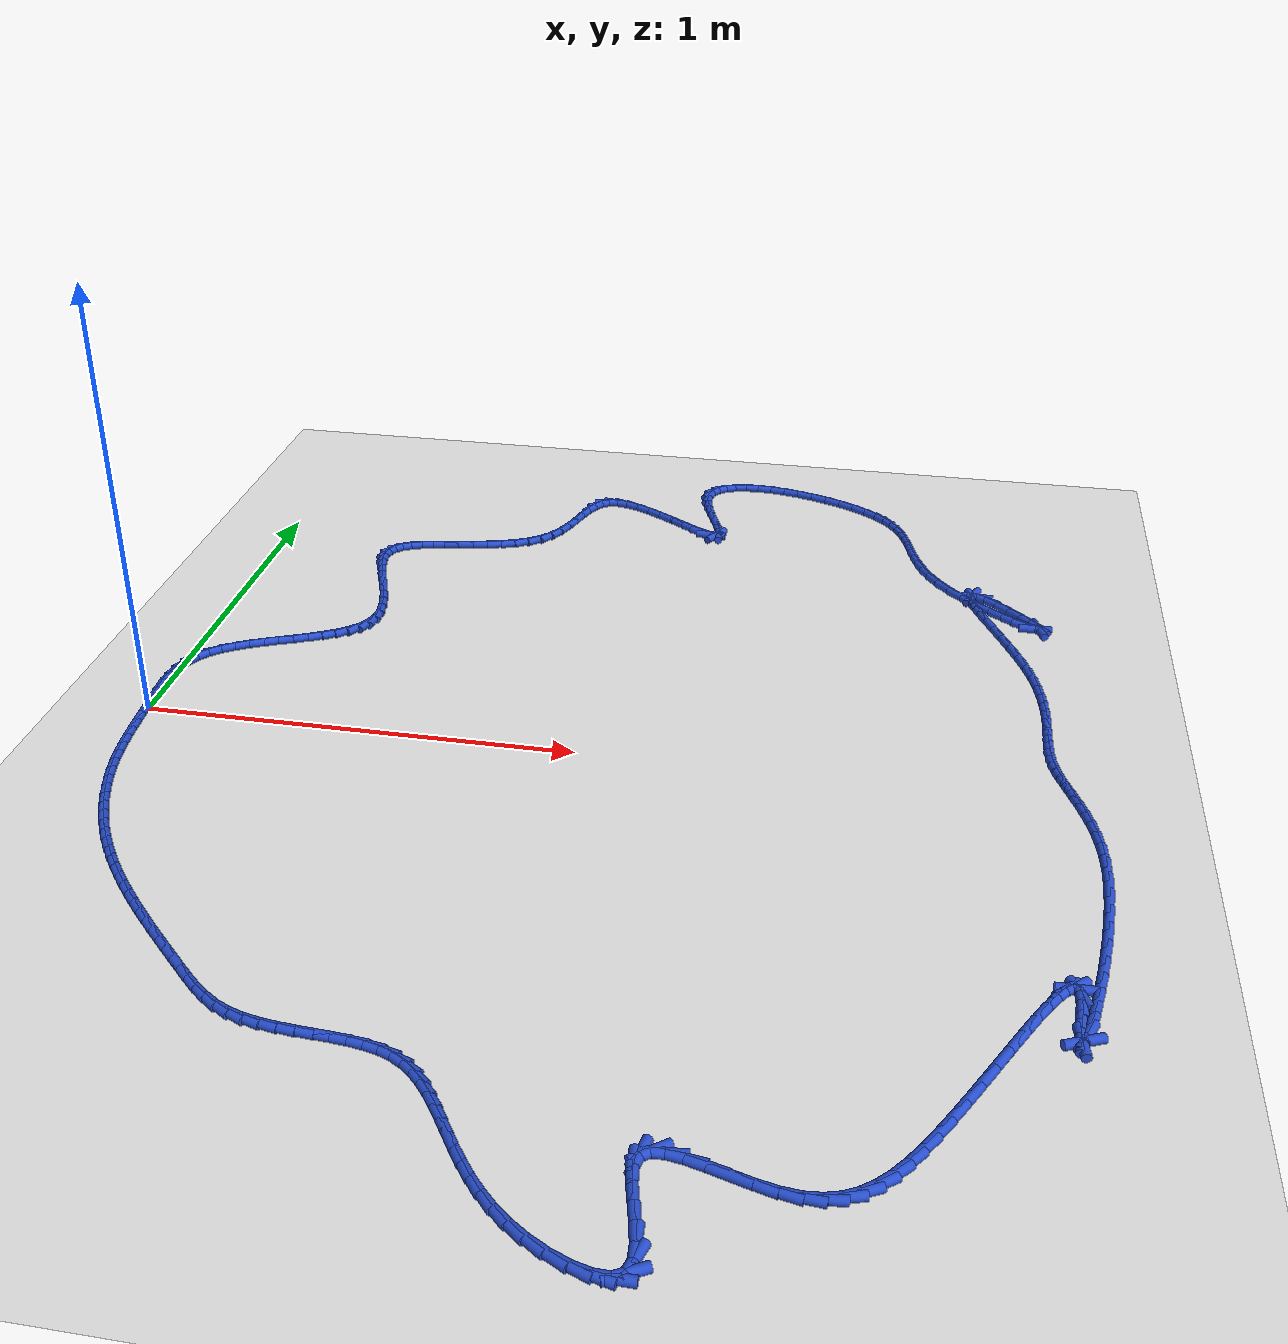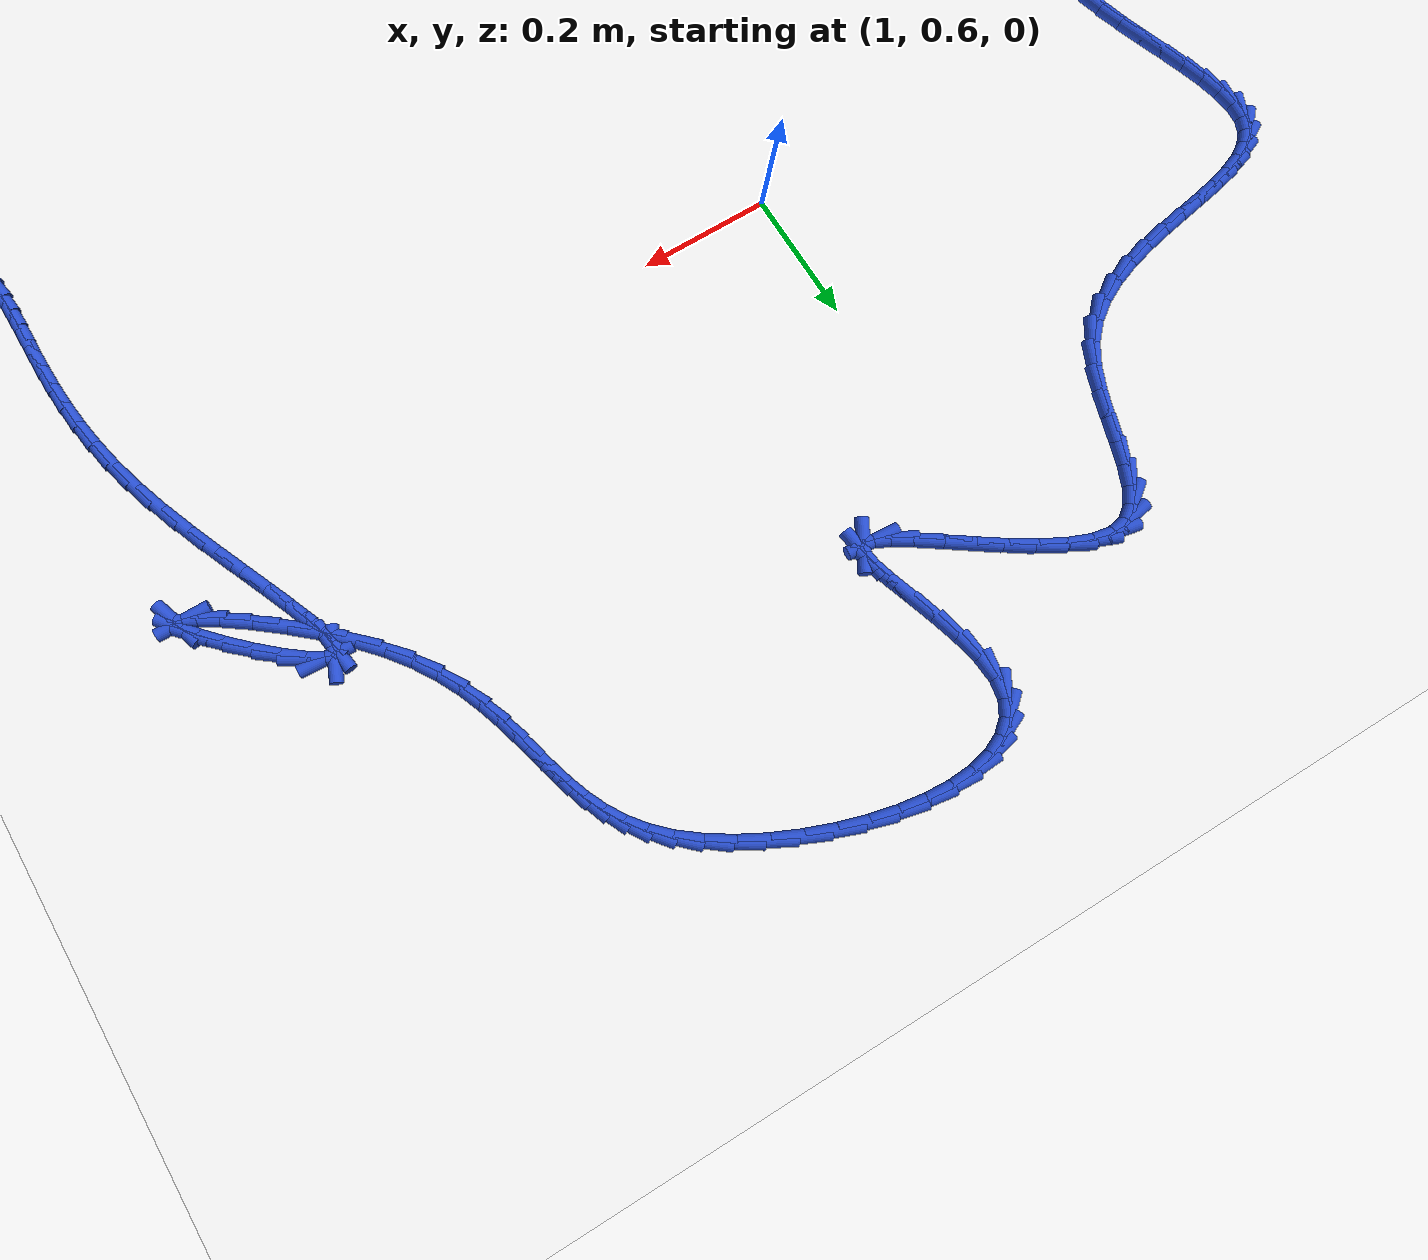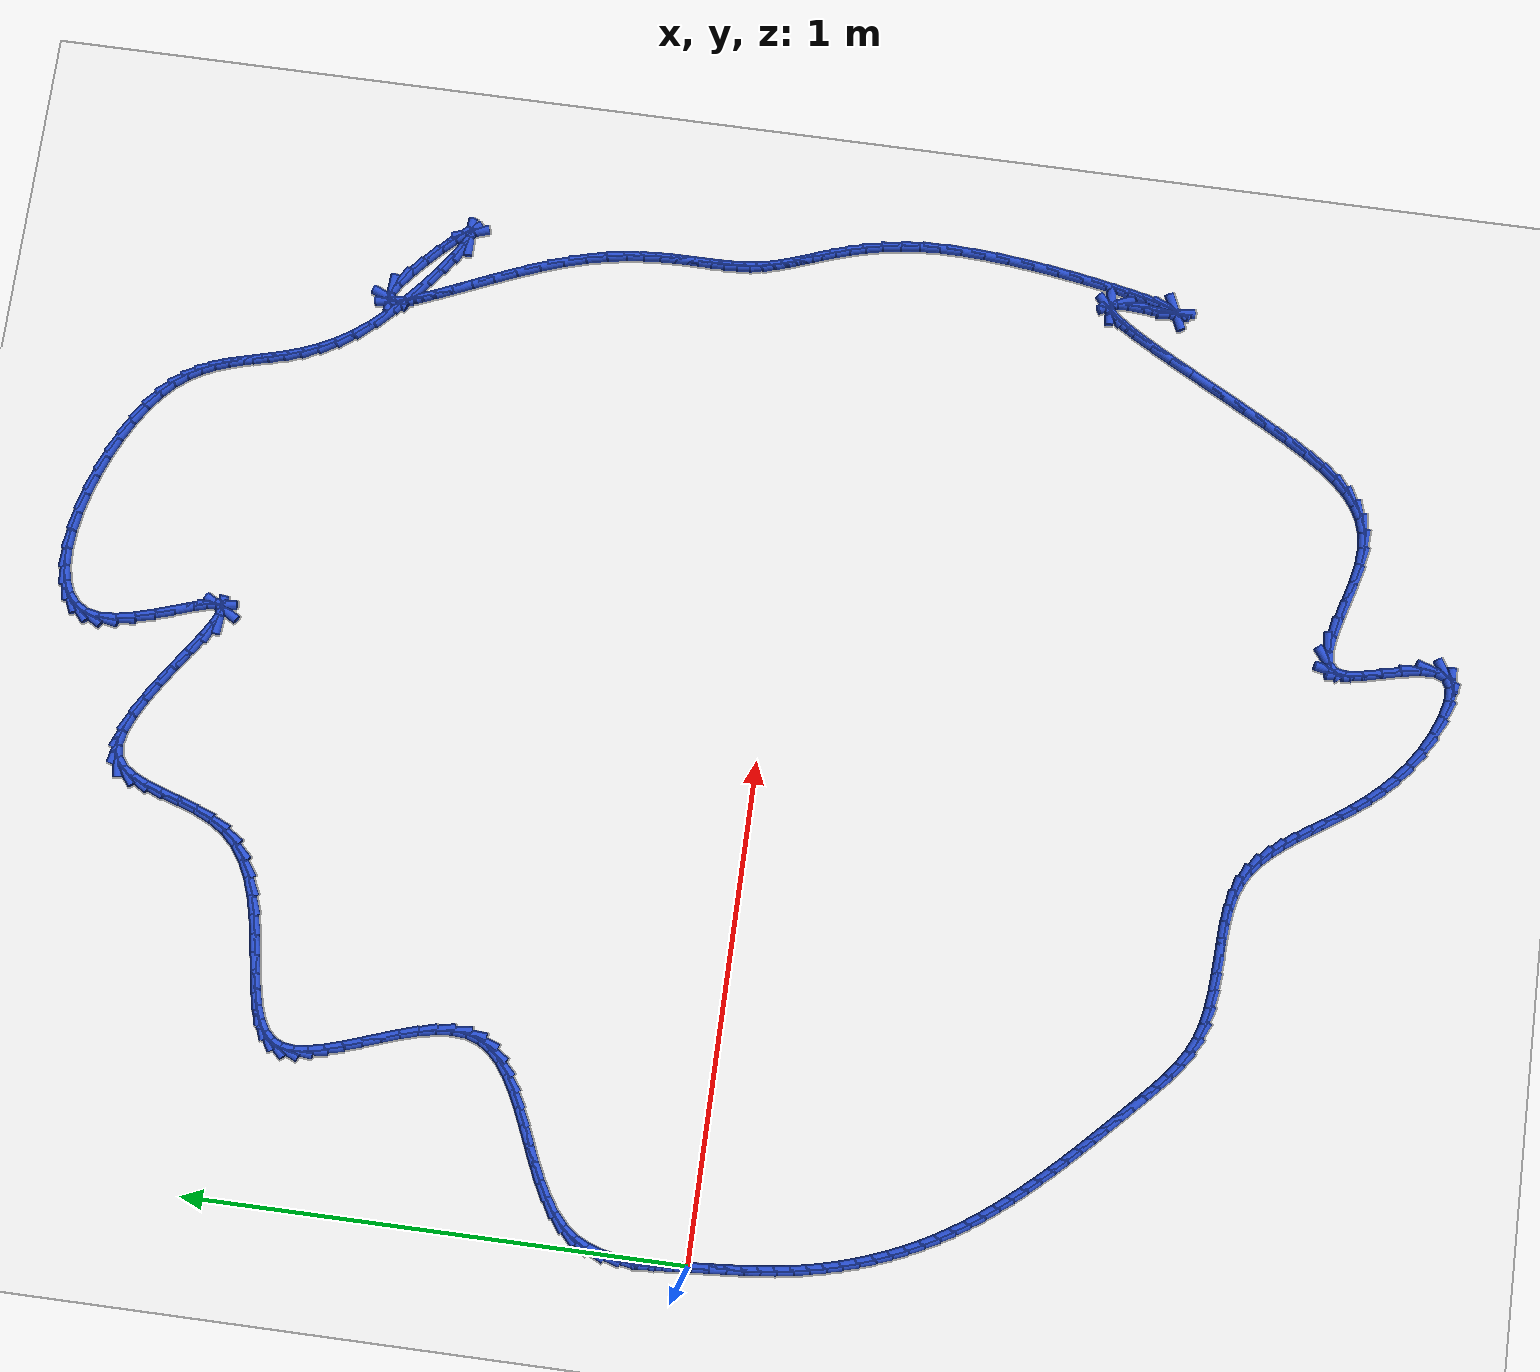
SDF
<sdf version="1.6">
 <world name="default">
  <light name="sun" type="directional">
   <pose>0 0 10 0 -0 0</pose>
   <diffuse>0.8 0.8 0.8 1</diffuse>
   <specular>0.2 0.2 0.2 1</specular>
   <attenuation>
    <range>1000</range>
    <constant>0.9</constant>
    <linear>0.01</linear>
    <quadratic>0.001</quadratic>
   </attenuation>
   <direction>-0.5 0.1 -0.9</direction>
  </light>
  <model name="ground_plane">
   <static>1</static>
   <link name="link">
    <collision name="collision">
     <geometry><plane><normal>0 0 1</normal><size>100 100</size></plane></geometry>
     <surface><friction><ode><mu>100</mu><mu2>50</mu2></ode></friction></surface>
    </collision>
    <visual name="visual">
     <cast_shadows>0</cast_shadows>
     <geometry><plane><normal>0 0 1</normal><size>100 100</size></plane></geometry>
     <material>
      <script><uri>file://media/materials/scripts/gazebo.material</uri><name>Gazebo/WhiteGlow</name></script>
     </material>
    </visual>
   </link>
  </model>
  <gravity>0 0 -9.8</gravity>
  <magnetic_field>6e-06 2.3e-05 -4.2e-05</magnetic_field>
  <atmosphere type="adiabatic"/>
  <physics name="default_physics" default="0" type="ode">
   <max_step_size>0.001</max_step_size>
   <real_time_factor>1</real_time_factor>
   <real_time_update_rate>1000</real_time_update_rate>
  </physics>
  <scene><ambient>0.4 0.4 0.4 1</ambient><background>0.7 0.7 0.7 1</background><shadows>1</shadows></scene>
  <spherical_coordinates>
   <surface_model>EARTH_WGS84</surface_model>
   <latitude_deg>0</latitude_deg>
   <longitude_deg>0</longitude_deg>
   <elevation>0</elevation>
   <heading_deg>0</heading_deg>
  </spherical_coordinates>
  <model name="line">
   <link name="link_0">
    <pose>2.6020852139652106e-18 -7.632783294297951e-17 0.01 0 1.57 -1.4976919063969427</pose>
    <collision name="collision">
     <geometry><cylinder><radius>0.01</radius><length>0.08</length></cylinder></geometry>
    </collision>
    <visual name="visual">
     <material>
      <script><name>Gazebo/Blue</name><uri>file://media/materials/scripts/gazebo.material</uri></script>
     </material>
     <geometry><cylinder><radius>0.01</radius><length>0.08</length></cylinder></geometry>
    </visual>
   </link>
   <link name="link_1">
    <pose>-0.0025229704079398315 0.034450370104736915 0.01 0 1.57 -1.5170141766266896</pose>
    <collision name="collision">
     <geometry><cylinder><radius>0.01</radius><length>0.08</length></cylinder></geometry>
    </collision>
    <visual name="visual">
     <material>
      <script><name>Gazebo/Blue</name><uri>file://media/materials/scripts/gazebo.material</uri></script>
     </material>
     <geometry><cylinder><radius>0.01</radius><length>0.08</length></cylinder></geometry>
    </visual>
   </link>
   <link name="link_2">
    <pose>-0.004391296338541851 0.06915564290359918 0.01 0 1.57 -1.5589634915492212</pose>
    <collision name="collision">
     <geometry><cylinder><radius>0.01</radius><length>0.08</length></cylinder></geometry>
    </collision>
    <visual name="visual">
     <material>
      <script><name>Gazebo/Blue</name><uri>file://media/materials/scripts/gazebo.material</uri></script>
     </material>
     <geometry><cylinder><radius>0.01</radius><length>0.08</length></cylinder></geometry>
    </visual>
   </link>
   <link name="link_3">
    <pose>-0.004798241237328891 0.10354519513095031 0.01 0 1.57 1.515301293113764</pose>
    <collision name="collision">
     <geometry><cylinder><radius>0.01</radius><length>0.08</length></cylinder></geometry>
    </collision>
    <visual name="visual">
     <material>
      <script><name>Gazebo/Blue</name><uri>file://media/materials/scripts/gazebo.material</uri></script>
     </material>
     <geometry><cylinder><radius>0.01</radius><length>0.08</length></cylinder></geometry>
    </visual>
   </link>
   <link name="link_4">
    <pose>-0.0029370685498237925 0.137048403521154 0.01 0 1.57 1.4179691063453683</pose>
    <collision name="collision">
     <geometry><cylinder><radius>0.01</radius><length>0.08</length></cylinder></geometry>
    </collision>
    <visual name="visual">
     <material>
      <script><name>Gazebo/Blue</name><uri>file://media/materials/scripts/gazebo.material</uri></script>
     </material>
     <geometry><cylinder><radius>0.01</radius><length>0.08</length></cylinder></geometry>
    </visual>
   </link>
   <link name="link_5">
    <pose>0.001998958278450603 0.16909464480857384 0.01 0 1.57 1.2850943708031755</pose>
    <collision name="collision">
     <geometry><cylinder><radius>0.01</radius><length>0.08</length></cylinder></geometry>
    </collision>
    <visual name="visual">
     <material>
      <script><name>Gazebo/Blue</name><uri>file://media/materials/scripts/gazebo.material</uri></script>
     </material>
     <geometry><cylinder><radius>0.01</radius><length>0.08</length></cylinder></geometry>
    </visual>
   </link>
   <link name="link_6">
    <pose>0.010816575801971469 0.1991132957275735 0.01 0 1.57 1.1131262142818894</pose>
    <collision name="collision">
     <geometry><cylinder><radius>0.01</radius><length>0.08</length></cylinder></geometry>
    </collision>
    <visual name="visual">
     <material>
      <script><name>Gazebo/Blue</name><uri>file://media/materials/scripts/gazebo.material</uri></script>
     </material>
     <geometry><cylinder><radius>0.01</radius><length>0.08</length></cylinder></geometry>
    </visual>
   </link>
   <link name="link_7">
    <pose>0.02432252057521597 0.22653373301251667 0.01 0 1.57 0.912755148140058</pose>
    <collision name="collision">
     <geometry><cylinder><radius>0.01</radius><length>0.08</length></cylinder></geometry>
    </collision>
    <visual name="visual">
     <material>
      <script><name>Gazebo/Blue</name><uri>file://media/materials/scripts/gazebo.material</uri></script>
     </material>
     <geometry><cylinder><radius>0.01</radius><length>0.08</length></cylinder></geometry>
    </visual>
   </link>
   <link name="link_8">
    <pose>0.04315058680638629 0.2508917836698029 0.01 0 1.57 0.7380858928481054</pose>
    <collision name="collision">
     <geometry><cylinder><radius>0.01</radius><length>0.08</length></cylinder></geometry>
    </collision>
    <visual name="visual">
     <material>
      <script><name>Gazebo/Blue</name><uri>file://media/materials/scripts/gazebo.material</uri></script>
     </material>
     <geometry><cylinder><radius>0.01</radius><length>0.08</length></cylinder></geometry>
    </visual>
   </link>
   <link name="link_9">
    <pose>0.06681224707028963 0.272414091303156 0.01 0 1.57 0.6082317110557185</pose>
    <collision name="collision">
     <geometry><cylinder><radius>0.01</radius><length>0.08</length></cylinder></geometry>
    </collision>
    <visual name="visual">
     <material>
      <script><name>Gazebo/Blue</name><uri>file://media/materials/scripts/gazebo.material</uri></script>
     </material>
     <geometry><cylinder><radius>0.01</radius><length>0.08</length></cylinder></geometry>
    </visual>
   </link>
   <link name="link_10">
    <pose>0.09437104744143045 0.2916030093053501 0.01 0 1.57 0.5171569191798234</pose>
    <collision name="collision">
     <geometry><cylinder><radius>0.01</radius><length>0.08</length></cylinder></geometry>
    </collision>
    <visual name="visual">
     <material>
      <script><name>Gazebo/Blue</name><uri>file://media/materials/scripts/gazebo.material</uri></script>
     </material>
     <geometry><cylinder><radius>0.01</radius><length>0.08</length></cylinder></geometry>
    </visual>
   </link>
   <link name="link_11">
    <pose>0.12488936577738169 0.3089616101354428 0.01 0 1.57 0.4577607158504061</pose>
    <collision name="collision">
     <geometry><cylinder><radius>0.01</radius><length>0.08</length></cylinder></geometry>
    </collision>
    <visual name="visual">
     <material>
      <script><name>Gazebo/Blue</name><uri>file://media/materials/scripts/gazebo.material</uri></script>
     </material>
     <geometry><cylinder><radius>0.01</radius><length>0.08</length></cylinder></geometry>
    </visual>
   </link>
   <link name="link_12">
    <pose>0.1574295799357159 0.3249929662524916 0.01 0 1.57 0.4247360248727408</pose>
    <collision name="collision">
     <geometry><cylinder><radius>0.01</radius><length>0.08</length></cylinder></geometry>
    </collision>
    <visual name="visual">
     <material>
      <script><name>Gazebo/Blue</name><uri>file://media/materials/scripts/gazebo.material</uri></script>
     </material>
     <geometry><cylinder><radius>0.01</radius><length>0.08</length></cylinder></geometry>
    </visual>
   </link>
   <link name="link_13">
    <pose>0.191054067774006 0.34020015011555427 0.01 0 1.57 0.4151711122764104</pose>
    <collision name="collision">
     <geometry><cylinder><radius>0.01</radius><length>0.08</length></cylinder></geometry>
    </collision>
    <visual name="visual">
     <material>
      <script><name>Gazebo/Blue</name><uri>file://media/materials/scripts/gazebo.material</uri></script>
     </material>
     <geometry><cylinder><radius>0.01</radius><length>0.08</length></cylinder></geometry>
    </visual>
   </link>
   <link name="link_14">
    <pose>0.22482520714982485 0.3550862341836883 0.01 0 1.57 0.4285625223447429</pose>
    <collision name="collision">
     <geometry><cylinder><radius>0.01</radius><length>0.08</length></cylinder></geometry>
    </collision>
    <visual name="visual">
     <material>
      <script><name>Gazebo/Blue</name><uri>file://media/materials/scripts/gazebo.material</uri></script>
     </material>
     <geometry><cylinder><radius>0.01</radius><length>0.08</length></cylinder></geometry>
    </visual>
   </link>
   <link name="link_15">
    <pose>0.25780537592074504 0.3701542909159514 0.01 0 1.57 0.4669013654232105</pose>
    <collision name="collision">
     <geometry><cylinder><radius>0.01</radius><length>0.08</length></cylinder></geometry>
    </collision>
    <visual name="visual">
     <material>
      <script><name>Gazebo/Blue</name><uri>file://media/materials/scripts/gazebo.material</uri></script>
     </material>
     <geometry><cylinder><radius>0.01</radius><length>0.08</length></cylinder></geometry>
    </visual>
   </link>
   <link name="link_16">
    <pose>0.28905695194433934 0.385907392771401 0.01 0 1.57 0.5350002826190938</pose>
    <collision name="collision">
     <geometry><cylinder><radius>0.01</radius><length>0.08</length></cylinder></geometry>
    </collision>
    <visual name="visual">
     <material>
      <script><name>Gazebo/Blue</name><uri>file://media/materials/scripts/gazebo.material</uri></script>
     </material>
     <geometry><cylinder><radius>0.01</radius><length>0.08</length></cylinder></geometry>
    </visual>
   </link>
   <link name="link_17">
    <pose>0.3176423130781808 0.402848612209095 0.01 0 1.57 0.6408382634927831</pose>
    <collision name="collision">
     <geometry><cylinder><radius>0.01</radius><length>0.08</length></cylinder></geometry>
    </collision>
    <visual name="visual">
     <material>
      <script><name>Gazebo/Blue</name><uri>file://media/materials/scripts/gazebo.material</uri></script>
     </material>
     <geometry><cylinder><radius>0.01</radius><length>0.08</length></cylinder></geometry>
    </visual>
   </link>
   <link name="link_18">
    <pose>0.34262383717984185 0.42148102168809076 0.01 0 1.57 0.794766380300998</pose>
    <collision name="collision">
     <geometry><cylinder><radius>0.01</radius><length>0.08</length></cylinder></geometry>
    </collision>
    <visual name="visual">
     <material>
      <script><name>Gazebo/Blue</name><uri>file://media/materials/scripts/gazebo.material</uri></script>
     </material>
     <geometry><cylinder><radius>0.01</radius><length>0.08</length></cylinder></geometry>
    </visual>
   </link>
   <link name="link_19">
    <pose>0.36306390210689554 0.44230769366744604 0.01 0 1.57 1.004334595589213</pose>
    <collision name="collision">
     <geometry><cylinder><radius>0.01</radius><length>0.08</length></cylinder></geometry>
    </collision>
    <visual name="visual">
     <material>
      <script><name>Gazebo/Blue</name><uri>file://media/materials/scripts/gazebo.material</uri></script>
     </material>
     <geometry><cylinder><radius>0.01</radius><length>0.08</length></cylinder></geometry>
    </visual>
   </link>
   <link name="link_20">
    <pose>0.3780248857169144 0.46583170060621826 0.01 0 1.57 1.2606739714048936</pose>
    <collision name="collision">
     <geometry><cylinder><radius>0.01</radius><length>0.08</length></cylinder></geometry>
    </collision>
    <visual name="visual">
     <material>
      <script><name>Gazebo/Blue</name><uri>file://media/materials/scripts/gazebo.material</uri></script>
     </material>
     <geometry><cylinder><radius>0.01</radius><length>0.08</length></cylinder></geometry>
    </visual>
   </link>
   <link name="link_21">
    <pose>0.3865860484981557 0.49254672936063276 0.01 0 1.57 1.5016194777007026</pose>
    <collision name="collision">
     <geometry><cylinder><radius>0.01</radius><length>0.08</length></cylinder></geometry>
    </collision>
    <visual name="visual">
     <material>
      <script><name>Gazebo/Blue</name><uri>file://media/materials/scripts/gazebo.material</uri></script>
     </material>
     <geometry><cylinder><radius>0.01</radius><length>0.08</length></cylinder></geometry>
    </visual>
   </link>
   <link name="link_22">
    <pose>0.3886602577044926 0.522483037706042 0.01 0 1.57 -1.469624507470114</pose>
    <collision name="collision">
     <geometry><cylinder><radius>0.01</radius><length>0.08</length></cylinder></geometry>
    </collision>
    <visual name="visual">
     <material>
      <script><name>Gazebo/Blue</name><uri>file://media/materials/scripts/gazebo.material</uri></script>
     </material>
     <geometry><cylinder><radius>0.01</radius><length>0.08</length></cylinder></geometry>
    </visual>
   </link>
   <link name="link_23">
    <pose>0.3853587103914075 0.5550046929531245 0.01 0 1.57 -1.3569918511122476</pose>
    <collision name="collision">
     <geometry><cylinder><radius>0.01</radius><length>0.08</length></cylinder></geometry>
    </collision>
    <visual name="visual">
     <material>
      <script><name>Gazebo/Blue</name><uri>file://media/materials/scripts/gazebo.material</uri></script>
     </material>
     <geometry><cylinder><radius>0.01</radius><length>0.08</length></cylinder></geometry>
    </visual>
   </link>
   <link name="link_24">
    <pose>0.37788545608997237 0.5894241427050492 0.01 0 1.57 -1.2857373610418217</pose>
    <collision name="collision">
     <geometry><cylinder><radius>0.01</radius><length>0.08</length></cylinder></geometry>
    </collision>
    <visual name="visual">
     <material>
      <script><name>Gazebo/Blue</name><uri>file://media/materials/scripts/gazebo.material</uri></script>
     </material>
     <geometry><cylinder><radius>0.01</radius><length>0.08</length></cylinder></geometry>
    </visual>
   </link>
   <link name="link_25">
    <pose>0.367444544331259 0.6250538345649849 0.01 0 1.57 -1.2452237197164782</pose>
    <collision name="collision">
     <geometry><cylinder><radius>0.01</radius><length>0.08</length></cylinder></geometry>
    </collision>
    <visual name="visual">
     <material>
      <script><name>Gazebo/Blue</name><uri>file://media/materials/scripts/gazebo.material</uri></script>
     </material>
     <geometry><cylinder><radius>0.01</radius><length>0.08</length></cylinder></geometry>
    </visual>
   </link>
   <link name="link_26">
    <pose>0.35524002464633925 0.6612062161361008 0.01 0 1.57 -1.2299577273898759</pose>
    <collision name="collision">
     <geometry><cylinder><radius>0.01</radius><length>0.08</length></cylinder></geometry>
    </collision>
    <visual name="visual">
     <material>
      <script><name>Gazebo/Blue</name><uri>file://media/materials/scripts/gazebo.material</uri></script>
     </material>
     <geometry><cylinder><radius>0.01</radius><length>0.08</length></cylinder></geometry>
    </visual>
   </link>
   <link name="link_27">
    <pose>0.3424759465662848 0.6971937350215658 0.01 0 1.57 -1.2386342525289127</pose>
    <collision name="collision">
     <geometry><cylinder><radius>0.01</radius><length>0.08</length></cylinder></geometry>
    </collision>
    <visual name="visual">
     <material>
      <script><name>Gazebo/Blue</name><uri>file://media/materials/scripts/gazebo.material</uri></script>
     </material>
     <geometry><cylinder><radius>0.01</radius><length>0.08</length></cylinder></geometry>
    </visual>
   </link>
   <link name="link_28">
    <pose>0.3303563596221676 0.7323288388245488 0.01 0 1.57 -1.2740908342791253</pose>
    <collision name="collision">
     <geometry><cylinder><radius>0.01</radius><length>0.08</length></cylinder></geometry>
    </collision>
    <visual name="visual">
     <material>
      <script><name>Gazebo/Blue</name><uri>file://media/materials/scripts/gazebo.material</uri></script>
     </material>
     <geometry><cylinder><radius>0.01</radius><length>0.08</length></cylinder></geometry>
    </visual>
   </link>
   <link name="link_29">
    <pose>0.3200853133450595 0.7659239751482189 0.01 0 1.57 -1.3446097266032184</pose>
    <collision name="collision">
     <geometry><cylinder><radius>0.01</radius><length>0.08</length></cylinder></geometry>
    </collision>
    <visual name="visual">
     <material>
      <script><name>Gazebo/Blue</name><uri>file://media/materials/scripts/gazebo.material</uri></script>
     </material>
     <geometry><cylinder><radius>0.01</radius><length>0.08</length></cylinder></geometry>
    </visual>
   </link>
   <link name="link_30">
    <pose>0.3128668572660322 0.797291591595745 0.01 0 1.57 -1.4670731887423112</pose>
    <collision name="collision">
     <geometry><cylinder><radius>0.01</radius><length>0.08</length></cylinder></geometry>
    </collision>
    <visual name="visual">
     <material>
      <script><name>Gazebo/Blue</name><uri>file://media/materials/scripts/gazebo.material</uri></script>
     </material>
     <geometry><cylinder><radius>0.01</radius><length>0.08</length></cylinder></geometry>
    </visual>
   </link>
   <link name="link_31">
    <pose>0.3099050409161575 0.8257441357702957 0.01 0 1.57 1.4705746438133722</pose>
    <collision name="collision">
     <geometry><cylinder><radius>0.01</radius><length>0.08</length></cylinder></geometry>
    </collision>
    <visual name="visual">
     <material>
      <script><name>Gazebo/Blue</name><uri>file://media/materials/scripts/gazebo.material</uri></script>
     </material>
     <geometry><cylinder><radius>0.01</radius><length>0.08</length></cylinder></geometry>
    </visual>
   </link>
   <link name="link_32">
    <pose>0.3124039138265074 0.8505940552750406 0.01 0 1.57 1.153549362429377</pose>
    <collision name="collision">
     <geometry><cylinder><radius>0.01</radius><length>0.08</length></cylinder></geometry>
    </collision>
    <visual name="visual">
     <material>
      <script><name>Gazebo/Blue</name><uri>file://media/materials/scripts/gazebo.material</uri></script>
     </material>
     <geometry><cylinder><radius>0.01</radius><length>0.08</length></cylinder></geometry>
    </visual>
   </link>
   <link name="link_33">
    <pose>0.32152912092665425 0.8711799598083261 0.01 0 1.57 0.7983372861386757</pose>
    <collision name="collision">
     <geometry><cylinder><radius>0.01</radius><length>0.08</length></cylinder></geometry>
    </collision>
    <visual name="visual">
     <material>
      <script><name>Gazebo/Blue</name><uri>file://media/materials/scripts/gazebo.material</uri></script>
     </material>
     <geometry><cylinder><radius>0.01</radius><length>0.08</length></cylinder></geometry>
    </visual>
   </link>
   <link name="link_34">
    <pose>0.3374505262752971 0.8875188078314787 0.01 0 1.57 0.5315350479991833</pose>
    <collision name="collision">
     <geometry><cylinder><radius>0.01</radius><length>0.08</length></cylinder></geometry>
    </collision>
    <visual name="visual">
     <material>
      <script><name>Gazebo/Blue</name><uri>file://media/materials/scripts/gazebo.material</uri></script>
     </material>
     <geometry><cylinder><radius>0.01</radius><length>0.08</length></cylinder></geometry>
    </visual>
   </link>
   <link name="link_35">
    <pose>0.35927540351605197 0.9003514187622974 0.01 0 1.57 0.36068515970582293</pose>
    <collision name="collision">
     <geometry><cylinder><radius>0.01</radius><length>0.08</length></cylinder></geometry>
    </collision>
    <visual name="visual">
     <material>
      <script><name>Gazebo/Blue</name><uri>file://media/materials/scripts/gazebo.material</uri></script>
     </material>
     <geometry><cylinder><radius>0.01</radius><length>0.08</length></cylinder></geometry>
    </visual>
   </link>
   <link name="link_36">
    <pose>0.38605924211632514 0.9104538885868513 0.01 0 1.57 0.25864758303891344</pose>
    <collision name="collision">
     <geometry><cylinder><radius>0.01</radius><length>0.08</length></cylinder></geometry>
    </collision>
    <visual name="visual">
     <material>
      <script><name>Gazebo/Blue</name><uri>file://media/materials/scripts/gazebo.material</uri></script>
     </material>
     <geometry><cylinder><radius>0.01</radius><length>0.08</length></cylinder></geometry>
    </visual>
   </link>
   <link name="link_37">
    <pose>0.4168575315435216 0.9186023132912106 0.01 0 1.57 0.2029773694061563</pose>
    <collision name="collision">
     <geometry><cylinder><radius>0.01</radius><length>0.08</length></cylinder></geometry>
    </collision>
    <visual name="visual">
     <material>
      <script><name>Gazebo/Blue</name><uri>file://media/materials/scripts/gazebo.material</uri></script>
     </material>
     <geometry><cylinder><radius>0.01</radius><length>0.08</length></cylinder></geometry>
    </visual>
   </link>
   <link name="link_38">
    <pose>0.4507257612650472 0.9255727888614441 0.01 0 1.57 0.18050749366841143</pose>
    <collision name="collision">
     <geometry><cylinder><radius>0.01</radius><length>0.08</length></cylinder></geometry>
    </collision>
    <visual name="visual">
     <material>
      <script><name>Gazebo/Blue</name><uri>file://media/materials/scripts/gazebo.material</uri></script>
     </material>
     <geometry><cylinder><radius>0.01</radius><length>0.08</length></cylinder></geometry>
    </visual>
   </link>
   <link name="link_39">
    <pose>0.48671942074830754 0.9321414112836219 0.01 0 1.57 0.1846366498743513</pose>
    <collision name="collision">
     <geometry><cylinder><radius>0.01</radius><length>0.08</length></cylinder></geometry>
    </collision>
    <visual name="visual">
     <material>
      <script><name>Gazebo/Blue</name><uri>file://media/materials/scripts/gazebo.material</uri></script>
     </material>
     <geometry><cylinder><radius>0.01</radius><length>0.08</length></cylinder></geometry>
    </visual>
   </link>
   <link name="link_40">
    <pose>0.5238939994607079 0.9390842765438132 0.01 0 1.57 0.21304922407864987</pose>
    <collision name="collision">
     <geometry><cylinder><radius>0.01</radius><length>0.08</length></cylinder></geometry>
    </collision>
    <visual name="visual">
     <material>
      <script><name>Gazebo/Blue</name><uri>file://media/materials/scripts/gazebo.material</uri></script>
     </material>
     <geometry><cylinder><radius>0.01</radius><length>0.08</length></cylinder></geometry>
    </visual>
   </link>
   <link name="link_41">
    <pose>0.5613049868696542 0.9471774806280879 0.01 0 1.57 0.26649956743154773</pose>
    <collision name="collision">
     <geometry><cylinder><radius>0.01</radius><length>0.08</length></cylinder></geometry>
    </collision>
    <visual name="visual">
     <material>
      <script><name>Gazebo/Blue</name><uri>file://media/materials/scripts/gazebo.material</uri></script>
     </material>
     <geometry><cylinder><radius>0.01</radius><length>0.08</length></cylinder></geometry>
    </visual>
   </link>
   <link name="link_42">
    <pose>0.5980078724425522 0.9571971195225153 0.01 0 1.57 0.34818163231276467</pose>
    <collision name="collision">
     <geometry><cylinder><radius>0.01</radius><length>0.08</length></cylinder></geometry>
    </collision>
    <visual name="visual">
     <material>
      <script><name>Gazebo/Blue</name><uri>file://media/materials/scripts/gazebo.material</uri></script>
     </material>
     <geometry><cylinder><radius>0.01</radius><length>0.08</length></cylinder></geometry>
    </visual>
   </link>
   <link name="link_43">
    <pose>0.6330581456468071 0.9699192892131655 0.01 0 1.57 0.46301193897874454</pose>
    <collision name="collision">
     <geometry><cylinder><radius>0.01</radius><length>0.08</length></cylinder></geometry>
    </collision>
    <visual name="visual">
     <material>
      <script><name>Gazebo/Blue</name><uri>file://media/materials/scripts/gazebo.material</uri></script>
     </material>
     <geometry><cylinder><radius>0.01</radius><length>0.08</length></cylinder></geometry>
    </visual>
   </link>
   <link name="link_44">
    <pose>0.6655112959498244 0.9861200856861072 0.01 0 1.57 0.6157561213551858</pose>
    <collision name="collision">
     <geometry><cylinder><radius>0.01</radius><length>0.08</length></cylinder></geometry>
    </collision>
    <visual name="visual">
     <material>
      <script><name>Gazebo/Blue</name><uri>file://media/materials/scripts/gazebo.material</uri></script>
     </material>
     <geometry><cylinder><radius>0.01</radius><length>0.08</length></cylinder></geometry>
    </visual>
   </link>
   <link name="link_45">
    <pose>0.6944228128190102 1.0065756049274106 0.01 0 1.57 0.8066515519919774</pose>
    <collision name="collision">
     <geometry><cylinder><radius>0.01</radius><length>0.08</length></cylinder></geometry>
    </collision>
    <visual name="visual">
     <material>
      <script><name>Gazebo/Blue</name><uri>file://media/materials/scripts/gazebo.material</uri></script>
     </material>
     <geometry><cylinder><radius>0.01</radius><length>0.08</length></cylinder></geometry>
    </visual>
   </link>
   <link name="link_46">
    <pose>0.7188481913079522 1.0320619361290564 0.01 0 1.57 1.0084744067232623</pose>
    <collision name="collision">
     <geometry><cylinder><radius>0.01</radius><length>0.08</length></cylinder></geometry>
    </collision>
    <visual name="visual">
     <material>
      <script><name>Gazebo/Blue</name><uri>file://media/materials/scripts/gazebo.material</uri></script>
     </material>
     <geometry><cylinder><radius>0.01</radius><length>0.08</length></cylinder></geometry>
    </visual>
   </link>
   <link name="link_47">
    <pose>0.738253868550962 1.062855368030787 0.01 0 1.57 1.1516465841817818</pose>
    <collision name="collision">
     <geometry><cylinder><radius>0.01</radius><length>0.08</length></cylinder></geometry>
    </collision>
    <visual name="visual">
     <material>
      <script><name>Gazebo/Blue</name><uri>file://media/materials/scripts/gazebo.material</uri></script>
     </material>
     <geometry><cylinder><radius>0.01</radius><length>0.08</length></cylinder></geometry>
    </visual>
   </link>
   <link name="link_48">
    <pose>0.7536338773376839 1.0973742803501427 0.01 0 1.57 1.2335720529055099</pose>
    <collision name="collision">
     <geometry><cylinder><radius>0.01</radius><length>0.08</length></cylinder></geometry>
    </collision>
    <visual name="visual">
     <material>
      <script><name>Gazebo/Blue</name><uri>file://media/materials/scripts/gazebo.material</uri></script>
     </material>
     <geometry><cylinder><radius>0.01</radius><length>0.08</length></cylinder></geometry>
    </visual>
   </link>
   <link name="link_49">
    <pose>0.7663371318305985 1.1336054351170264 0.01 0 1.57 1.2641824726305135</pose>
    <collision name="collision">
     <geometry><cylinder><radius>0.01</radius><length>0.08</length></cylinder></geometry>
    </collision>
    <visual name="visual">
     <material>
      <script><name>Gazebo/Blue</name><uri>file://media/materials/scripts/gazebo.material</uri></script>
     </material>
     <geometry><cylinder><radius>0.01</radius><length>0.08</length></cylinder></geometry>
    </visual>
   </link>
   <link name="link_50">
    <pose>0.7777125461921851 1.1695355943613415 0.01 0 1.57 1.2439360731924185</pose>
    <collision name="collision">
     <geometry><cylinder><radius>0.01</radius><length>0.08</length></cylinder></geometry>
    </collision>
    <visual name="visual">
     <material>
      <script><name>Gazebo/Blue</name><uri>file://media/materials/scripts/gazebo.material</uri></script>
     </material>
     <geometry><cylinder><radius>0.01</radius><length>0.08</length></cylinder></geometry>
    </visual>
   </link>
   <link name="link_51">
    <pose>0.7891090345849238 1.2031515201129905 0.01 0 1.57 1.15973997201001</pose>
    <collision name="collision">
     <geometry><cylinder><radius>0.01</radius><length>0.08</length></cylinder></geometry>
    </collision>
    <visual name="visual">
     <material>
      <script><name>Gazebo/Blue</name><uri>file://media/materials/scripts/gazebo.material</uri></script>
     </material>
     <geometry><cylinder><radius>0.01</radius><length>0.08</length></cylinder></geometry>
    </visual>
   </link>
   <link name="link_52">
    <pose>0.8018755111712947 1.2324399744018777 0.01 0 1.57 0.9771768632697877</pose>
    <collision name="collision">
     <geometry><cylinder><radius>0.01</radius><length>0.08</length></cylinder></geometry>
    </collision>
    <visual name="visual">
     <material>
      <script><name>Gazebo/Blue</name><uri>file://media/materials/scripts/gazebo.material</uri></script>
     </material>
     <geometry><cylinder><radius>0.01</radius><length>0.08</length></cylinder></geometry>
    </visual>
   </link>
   <link name="link_53">
    <pose>0.8173608901137775 1.2553877192579048 0.01 0 1.57 0.6411698822605154</pose>
    <collision name="collision">
     <geometry><cylinder><radius>0.01</radius><length>0.08</length></cylinder></geometry>
    </collision>
    <visual name="visual">
     <material>
      <script><name>Gazebo/Blue</name><uri>file://media/materials/scripts/gazebo.material</uri></script>
     </material>
     <geometry><cylinder><radius>0.01</radius><length>0.08</length></cylinder></geometry>
    </visual>
   </link>
   <link name="link_54">
    <pose>0.836914085574852 1.2699815167109751 0.01 0 1.57 0.1737670100095126</pose>
    <collision name="collision">
     <geometry><cylinder><radius>0.01</radius><length>0.08</length></cylinder></geometry>
    </collision>
    <visual name="visual">
     <material>
      <script><name>Gazebo/Blue</name><uri>file://media/materials/scripts/gazebo.material</uri></script>
     </material>
     <geometry><cylinder><radius>0.01</radius><length>0.08</length></cylinder></geometry>
    </visual>
   </link>
   <link name="link_55">
    <pose>0.8617907383984234 1.2743482986428687 0.01 0 1.57 -0.182812134037532</pose>
    <collision name="collision">
     <geometry><cylinder><radius>0.01</radius><length>0.08</length></cylinder></geometry>
    </collision>
    <visual name="visual">
     <material>
      <script><name>Gazebo/Blue</name><uri>file://media/materials/scripts/gazebo.material</uri></script>
     </material>
     <geometry><cylinder><radius>0.01</radius><length>0.08</length></cylinder></geometry>
    </visual>
   </link>
   <link name="link_56">
    <pose>0.8917912460740702 1.268801916501834 0.01 0 1.57 -0.3781019902746656</pose>
    <collision name="collision">
     <geometry><cylinder><radius>0.01</radius><length>0.08</length></cylinder></geometry>
    </collision>
    <visual name="visual">
     <material>
      <script><name>Gazebo/Blue</name><uri>file://media/materials/scripts/gazebo.material</uri></script>
     </material>
     <geometry><cylinder><radius>0.01</radius><length>0.08</length></cylinder></geometry>
    </visual>
   </link>
   <link name="link_57">
    <pose>0.9255644710024911 1.255386732725814 0.01 0 1.57 -0.4879142463259823</pose>
    <collision name="collision">
     <geometry><cylinder><radius>0.01</radius><length>0.08</length></cylinder></geometry>
    </collision>
    <visual name="visual">
     <material>
      <script><name>Gazebo/Blue</name><uri>file://media/materials/scripts/gazebo.material</uri></script>
     </material>
     <geometry><cylinder><radius>0.01</radius><length>0.08</length></cylinder></geometry>
    </visual>
   </link>
   <link name="link_58">
    <pose>0.9617277891304779 1.2361944271597862 0.01 0 1.57 -0.551721654150297</pose>
    <collision name="collision">
     <geometry><cylinder><radius>0.01</radius><length>0.08</length></cylinder></geometry>
    </collision>
    <visual name="visual">
     <material>
      <script><name>Gazebo/Blue</name><uri>file://media/materials/scripts/gazebo.material</uri></script>
     </material>
     <geometry><cylinder><radius>0.01</radius><length>0.08</length></cylinder></geometry>
    </visual>
   </link>
   <link name="link_59">
    <pose>0.9988985764048219 1.2133166796487287 0.01 0 1.57 -0.5868933590739235</pose>
    <collision name="collision">
     <geometry><cylinder><radius>0.01</radius><length>0.08</length></cylinder></geometry>
    </collision>
    <visual name="visual">
     <material>
      <script><name>Gazebo/Blue</name><uri>file://media/materials/scripts/gazebo.material</uri></script>
     </material>
     <geometry><cylinder><radius>0.01</radius><length>0.08</length></cylinder></geometry>
    </visual>
   </link>
   <link name="link_60">
    <pose>1.035694208772315 1.1888451700376186 0.01 0 1.57 -0.6000565069484108</pose>
    <collision name="collision">
     <geometry><cylinder><radius>0.01</radius><length>0.08</length></cylinder></geometry>
    </collision>
    <visual name="visual">
     <material>
      <script><name>Gazebo/Blue</name><uri>file://media/materials/scripts/gazebo.material</uri></script>
     </material>
     <geometry><cylinder><radius>0.01</radius><length>0.08</length></cylinder></geometry>
    </visual>
   </link>
   <link name="link_61">
    <pose>1.0707320621797478 1.1648715781714338 0.01 0 1.57 -0.5905815460054495</pose>
    <collision name="collision">
     <geometry><cylinder><radius>0.01</radius><length>0.08</length></cylinder></geometry>
    </collision>
    <visual name="visual">
     <material>
      <script><name>Gazebo/Blue</name><uri>file://media/materials/scripts/gazebo.material</uri></script>
     </material>
     <geometry><cylinder><radius>0.01</radius><length>0.08</length></cylinder></geometry>
    </visual>
   </link>
   <link name="link_62">
    <pose>1.1026295125739116 1.1434875838951513 0.01 0 1.57 -0.5478549832931016</pose>
    <collision name="collision">
     <geometry><cylinder><radius>0.01</radius><length>0.08</length></cylinder></geometry>
    </collision>
    <visual name="visual">
     <material>
      <script><name>Gazebo/Blue</name><uri>file://media/materials/scripts/gazebo.material</uri></script>
     </material>
     <geometry><cylinder><radius>0.01</radius><length>0.08</length></cylinder></geometry>
    </visual>
   </link>
   <link name="link_63">
    <pose>1.1300039359015983 1.1267848670537484 0.01 0 1.57 -0.43321752810237335</pose>
    <collision name="collision">
     <geometry><cylinder><radius>0.01</radius><length>0.08</length></cylinder></geometry>
    </collision>
    <visual name="visual">
     <material>
      <script><name>Gazebo/Blue</name><uri>file://media/materials/scripts/gazebo.material</uri></script>
     </material>
     <geometry><cylinder><radius>0.01</radius><length>0.08</length></cylinder></geometry>
    </visual>
   </link>
   <link name="link_64">
    <pose>1.1514727081096 1.1168551074922035 0.01 0 1.57 -0.07497100596428513</pose>
    <collision name="collision">
     <geometry><cylinder><radius>0.01</radius><length>0.08</length></cylinder></geometry>
    </collision>
    <visual name="visual">
     <material>
      <script><name>Gazebo/Blue</name><uri>file://media/materials/scripts/gazebo.material</uri></script>
     </material>
     <geometry><cylinder><radius>0.01</radius><length>0.08</length></cylinder></geometry>
    </visual>
   </link>
   <link name="link_65">
    <pose>1.1656532051447064 1.1157899850554933 0.01 0 1.57 1.0488969806824193</pose>
    <collision name="collision">
     <geometry><cylinder><radius>0.01</radius><length>0.08</length></cylinder></geometry>
    </collision>
    <visual name="visual">
     <material>
      <script><name>Gazebo/Blue</name><uri>file://media/materials/scripts/gazebo.material</uri></script>
     </material>
     <geometry><cylinder><radius>0.01</radius><length>0.08</length></cylinder></geometry>
    </visual>
   </link>
   <link name="link_66">
    <pose>1.171268219180254 1.125553756651792 0.01 0 1.57 -1.4558059415035038</pose>
    <collision name="collision">
     <geometry><cylinder><radius>0.01</radius><length>0.08</length></cylinder></geometry>
    </collision>
    <visual name="visual">
     <material>
      <script><name>Gazebo/Blue</name><uri>file://media/materials/scripts/gazebo.material</uri></script>
     </material>
     <geometry><cylinder><radius>0.01</radius><length>0.08</length></cylinder></geometry>
    </visual>
   </link>
   <link name="link_67">
    <pose>1.1689261494113907 1.1458314325091925 0.01 0 1.57 -1.295163826412042</pose>
    <collision name="collision">
     <geometry><cylinder><radius>0.01</radius><length>0.08</length></cylinder></geometry>
    </collision>
    <visual name="visual">
     <material>
      <script><name>Gazebo/Blue</name><uri>file://media/materials/scripts/gazebo.material</uri></script>
     </material>
     <geometry><cylinder><radius>0.01</radius><length>0.08</length></cylinder></geometry>
    </visual>
   </link>
   <link name="link_68">
    <pose>1.1608627649033894 1.1743409229612525 0.01 0 1.57 -1.248244478907562</pose>
    <collision name="collision">
     <geometry><cylinder><radius>0.01</radius><length>0.08</length></cylinder></geometry>
    </collision>
    <visual name="visual">
     <material>
      <script><name>Gazebo/Blue</name><uri>file://media/materials/scripts/gazebo.material</uri></script>
     </material>
     <geometry><cylinder><radius>0.01</radius><length>0.08</length></cylinder></geometry>
    </visual>
   </link>
   <link name="link_69">
    <pose>1.1493672520503915 1.2087355696015551 0.01 0 1.57 -1.2491863948866875</pose>
    <collision name="collision">
     <geometry><cylinder><radius>0.01</radius><length>0.08</length></cylinder></geometry>
    </collision>
    <visual name="visual">
     <material>
      <script><name>Gazebo/Blue</name><uri>file://media/materials/scripts/gazebo.material</uri></script>
     </material>
     <geometry><cylinder><radius>0.01</radius><length>0.08</length></cylinder></geometry>
    </visual>
   </link>
   <link name="link_70">
    <pose>1.1367287972465376 1.2466687140236865 0.01 0 1.57 -1.2851010266673877</pose>
    <collision name="collision">
     <geometry><cylinder><radius>0.01</radius><length>0.08</length></cylinder></geometry>
    </collision>
    <visual name="visual">
     <material>
      <script><name>Gazebo/Blue</name><uri>file://media/materials/scripts/gazebo.material</uri></script>
     </material>
     <geometry><cylinder><radius>0.01</radius><length>0.08</length></cylinder></geometry>
    </visual>
   </link>
   <link name="link_71">
    <pose>1.1252365868859682 1.285793697821232 0.01 0 1.57 -1.3617103245073632</pose>
    <collision name="collision">
     <geometry><cylinder><radius>0.01</radius><length>0.08</length></cylinder></geometry>
    </collision>
    <visual name="visual">
     <material>
      <script><name>Gazebo/Blue</name><uri>file://media/materials/scripts/gazebo.material</uri></script>
     </material>
     <geometry><cylinder><radius>0.01</radius><length>0.08</length></cylinder></geometry>
    </visual>
   </link>
   <link name="link_72">
    <pose>1.1171798073628234 1.3237638625877761 0.01 0 1.57 -1.5032389754969586</pose>
    <collision name="collision">
     <geometry><cylinder><radius>0.01</radius><length>0.08</length></cylinder></geometry>
    </collision>
    <visual name="visual">
     <material>
      <script><name>Gazebo/Blue</name><uri>file://media/materials/scripts/gazebo.material</uri></script>
     </material>
     <geometry><cylinder><radius>0.01</radius><length>0.08</length></cylinder></geometry>
    </visual>
   </link>
   <link name="link_73">
    <pose>1.114847645071245 1.3582325499169035 0.01 0 1.57 1.3844136864425602</pose>
    <collision name="collision">
     <geometry><cylinder><radius>0.01</radius><length>0.08</length></cylinder></geometry>
    </collision>
    <visual name="visual">
     <material>
      <script><name>Gazebo/Blue</name><uri>file://media/materials/scripts/gazebo.material</uri></script>
     </material>
     <geometry><cylinder><radius>0.01</radius><length>0.08</length></cylinder></geometry>
    </visual>
   </link>
   <link name="link_74">
    <pose>1.1202836796227331 1.387060029439835 0.01 0 1.57 1.0430162346590754</pose>
    <collision name="collision">
     <geometry><cylinder><radius>0.01</radius><length>0.08</length></cylinder></geometry>
    </collision>
    <visual name="visual">
     <material>
      <script><name>Gazebo/Blue</name><uri>file://media/materials/scripts/gazebo.material</uri></script>
     </material>
     <geometry><cylinder><radius>0.01</radius><length>0.08</length></cylinder></geometry>
    </visual>
   </link>
   <link name="link_75">
    <pose>1.1335337096160758 1.4097897364566747 0.01 0 1.57 0.7009519575726849</pose>
    <collision name="collision">
     <geometry><cylinder><radius>0.01</radius><length>0.08</length></cylinder></geometry>
    </collision>
    <visual name="visual">
     <material>
      <script><name>Gazebo/Blue</name><uri>file://media/materials/scripts/gazebo.material</uri></script>
     </material>
     <geometry><cylinder><radius>0.01</radius><length>0.08</length></cylinder></geometry>
    </visual>
   </link>
   <link name="link_76">
    <pose>1.1536713229481659 1.426784210897084 0.01 0 1.57 0.41920578496889355</pose>
    <collision name="collision">
     <geometry><cylinder><radius>0.01</radius><length>0.08</length></cylinder></geometry>
    </collision>
    <visual name="visual">
     <material>
      <script><name>Gazebo/Blue</name><uri>file://media/materials/scripts/gazebo.material</uri></script>
     </material>
     <geometry><cylinder><radius>0.01</radius><length>0.08</length></cylinder></geometry>
    </visual>
   </link>
   <link name="link_77">
    <pose>1.1797636129354085 1.438411464489104 0.01 0 1.57 0.20988679104183577</pose>
    <collision name="collision">
     <geometry><cylinder><radius>0.01</radius><length>0.08</length></cylinder></geometry>
    </collision>
    <visual name="visual">
     <material>
      <script><name>Gazebo/Blue</name><uri>file://media/materials/scripts/gazebo.material</uri></script>
     </material>
     <geometry><cylinder><radius>0.01</radius><length>0.08</length></cylinder></geometry>
    </visual>
   </link>
   <link name="link_78">
    <pose>1.21087767289421 1.4450395089607755 0.01 0 1.57 0.05666317836701319</pose>
    <collision name="collision">
     <geometry><cylinder><radius>0.01</radius><length>0.08</length></cylinder></geometry>
    </collision>
    <visual name="visual">
     <material>
      <script><name>Gazebo/Blue</name><uri>file://media/materials/scripts/gazebo.material</uri></script>
     </material>
     <geometry><cylinder><radius>0.01</radius><length>0.08</length></cylinder></geometry>
    </visual>
   </link>
   <link name="link_79">
    <pose>1.246080596140976 1.4470363560401402 0.01 0 1.57 -0.059013898095474616</pose>
    <collision name="collision">
     <geometry><cylinder><radius>0.01</radius><length>0.08</length></cylinder></geometry>
    </collision>
    <visual name="visual">
     <material>
      <script><name>Gazebo/Blue</name><uri>file://media/materials/scripts/gazebo.material</uri></script>
     </material>
     <geometry><cylinder><radius>0.01</radius><length>0.08</length></cylinder></geometry>
    </visual>
   </link>
   <link name="link_80">
    <pose>1.2844394759921116 1.4447700174552396 0.01 0 1.57 -0.15067818776980507</pose>
    <collision name="collision">
     <geometry><cylinder><radius>0.01</radius><length>0.08</length></cylinder></geometry>
    </collision>
    <visual name="visual">
     <material>
      <script><name>Gazebo/Blue</name><uri>file://media/materials/scripts/gazebo.material</uri></script>
     </material>
     <geometry><cylinder><radius>0.01</radius><length>0.08</length></cylinder></geometry>
    </visual>
   </link>
   <link name="link_81">
    <pose>1.3250214057640235 1.4386085049341142 0.01 0 1.57 -0.22738578678764337</pose>
    <collision name="collision">
     <geometry><cylinder><radius>0.01</radius><length>0.08</length></cylinder></geometry>
    </collision>
    <visual name="visual">
     <material>
      <script><name>Gazebo/Blue</name><uri>file://media/materials/scripts/gazebo.material</uri></script>
     </material>
     <geometry><cylinder><radius>0.01</radius><length>0.08</length></cylinder></geometry>
    </visual>
   </link>
   <link name="link_82">
    <pose>1.3668934787731175 1.4289198302048054 0.01 0 1.57 -0.29534171705395845</pose>
    <collision name="collision">
     <geometry><cylinder><radius>0.01</radius><length>0.08</length></cylinder></geometry>
    </collision>
    <visual name="visual">
     <material>
      <script><name>Gazebo/Blue</name><uri>file://media/materials/scripts/gazebo.material</uri></script>
     </material>
     <geometry><cylinder><radius>0.01</radius><length>0.08</length></cylinder></geometry>
    </visual>
   </link>
   <link name="link_83">
    <pose>1.409122788335799 1.416072004995355 0.01 0 1.57 -0.3591673425585128</pose>
    <collision name="collision">
     <geometry><cylinder><radius>0.01</radius><length>0.08</length></cylinder></geometry>
    </collision>
    <visual name="visual">
     <material>
      <script><name>Gazebo/Blue</name><uri>file://media/materials/scripts/gazebo.material</uri></script>
     </material>
     <geometry><cylinder><radius>0.01</radius><length>0.08</length></cylinder></geometry>
    </visual>
   </link>
   <link name="link_84">
    <pose>1.4507764277684734 1.4004330410338028 0.01 0 1.57 -0.422787901797771</pose>
    <collision name="collision">
     <geometry><cylinder><radius>0.01</radius><length>0.08</length></cylinder></geometry>
    </collision>
    <visual name="visual">
     <material>
      <script><name>Gazebo/Blue</name><uri>file://media/materials/scripts/gazebo.material</uri></script>
     </material>
     <geometry><cylinder><radius>0.01</radius><length>0.08</length></cylinder></geometry>
    </visual>
   </link>
   <link name="link_85">
    <pose>1.4909214903875467 1.3823709500481913 0.01 0 1.57 -0.4901355269306434</pose>
    <collision name="collision">
     <geometry><cylinder><radius>0.01</radius><length>0.08</length></cylinder></geometry>
    </collision>
    <visual name="visual">
     <material>
      <script><name>Gazebo/Blue</name><uri>file://media/materials/scripts/gazebo.material</uri></script>
     </material>
     <geometry><cylinder><radius>0.01</radius><length>0.08</length></cylinder></geometry>
    </visual>
   </link>
   <link name="link_86">
    <pose>1.5286250695094252 1.362253743766562 0.01 0 1.57 -0.5658675238807724</pose>
    <collision name="collision">
     <geometry><cylinder><radius>0.01</radius><length>0.08</length></cylinder></geometry>
    </collision>
    <visual name="visual">
     <material>
      <script><name>Gazebo/Blue</name><uri>file://media/materials/scripts/gazebo.material</uri></script>
     </material>
     <geometry><cylinder><radius>0.01</radius><length>0.08</length></cylinder></geometry>
    </visual>
   </link>
   <link name="link_87">
    <pose>1.5629542584505138 1.3404494339169546 0.01 0 1.57 -0.6563155612507883</pose>
    <collision name="collision">
     <geometry><cylinder><radius>0.01</radius><length>0.08</length></cylinder></geometry>
    </collision>
    <visual name="visual">
     <material>
      <script><name>Gazebo/Blue</name><uri>file://media/materials/scripts/gazebo.material</uri></script>
     </material>
     <geometry><cylinder><radius>0.01</radius><length>0.08</length></cylinder></geometry>
    </visual>
   </link>
   <link name="link_88">
    <pose>1.5929761505272186 1.3173260322274114 0.01 0 1.57 -0.769297263653076</pose>
    <collision name="collision">
     <geometry><cylinder><radius>0.01</radius><length>0.08</length></cylinder></geometry>
    </collision>
    <visual name="visual">
     <material>
      <script><name>Gazebo/Blue</name><uri>file://media/materials/scripts/gazebo.material</uri></script>
     </material>
     <geometry><cylinder><radius>0.01</radius><length>0.08</length></cylinder></geometry>
    </visual>
   </link>
   <link name="link_89">
    <pose>1.6178594171813907 1.2932314216160885 0.01 0 1.57 -0.8956313855214411</pose>
    <collision name="collision">
     <geometry><cylinder><radius>0.01</radius><length>0.08</length></cylinder></geometry>
    </collision>
    <visual name="visual">
     <material>
      <script><name>Gazebo/Blue</name><uri>file://media/materials/scripts/gazebo.material</uri></script>
     </material>
     <geometry><cylinder><radius>0.01</radius><length>0.08</length></cylinder></geometry>
    </visual>
   </link>
   <link name="link_90">
    <pose>1.6378165850158215 1.2683066337525157 0.01 0 1.57 -1.0185782493417879</pose>
    <collision name="collision">
     <geometry><cylinder><radius>0.01</radius><length>0.08</length></cylinder></geometry>
    </collision>
    <visual name="visual">
     <material>
      <script><name>Gazebo/Blue</name><uri>file://media/materials/scripts/gazebo.material</uri></script>
     </material>
     <geometry><cylinder><radius>0.01</radius><length>0.08</length></cylinder></geometry>
    </visual>
   </link>
   <link name="link_91">
    <pose>1.6536738226688912 1.2425711004655342 0.01 0 1.57 -1.1276453673470754</pose>
    <collision name="collision">
     <geometry><cylinder><radius>0.01</radius><length>0.08</length></cylinder></geometry>
    </collision>
    <visual name="visual">
     <material>
      <script><name>Gazebo/Blue</name><uri>file://media/materials/scripts/gazebo.material</uri></script>
     </material>
     <geometry><cylinder><radius>0.01</radius><length>0.08</length></cylinder></geometry>
    </visual>
   </link>
   <link name="link_92">
    <pose>1.6662651460626112 1.216042698559419 0.01 0 1.57 -1.2145759397727756</pose>
    <collision name="collision">
     <geometry><cylinder><radius>0.01</radius><length>0.08</length></cylinder></geometry>
    </collision>
    <visual name="visual">
     <material>
      <script><name>Gazebo/Blue</name><uri>file://media/materials/scripts/gazebo.material</uri></script>
     </material>
     <geometry><cylinder><radius>0.01</radius><length>0.08</length></cylinder></geometry>
    </visual>
   </link>
   <link name="link_93">
    <pose>1.6764245711189933 1.1887393048384471 0.01 0 1.57 -1.2746580504739031</pose>
    <collision name="collision">
     <geometry><cylinder><radius>0.01</radius><length>0.08</length></cylinder></geometry>
    </collision>
    <visual name="visual">
     <material>
      <script><name>Gazebo/Blue</name><uri>file://media/materials/scripts/gazebo.material</uri></script>
     </material>
     <geometry><cylinder><radius>0.01</radius><length>0.08</length></cylinder></geometry>
    </visual>
   </link>
   <link name="link_94">
    <pose>1.6849861137600481 1.1606787961068947 0.01 0 1.57 -1.30638090434193</pose>
    <collision name="collision">
     <geometry><cylinder><radius>0.01</radius><length>0.08</length></cylinder></geometry>
    </collision>
    <visual name="visual">
     <material>
      <script><name>Gazebo/Blue</name><uri>file://media/materials/scripts/gazebo.material</uri></script>
     </material>
     <geometry><cylinder><radius>0.01</radius><length>0.08</length></cylinder></geometry>
    </visual>
   </link>
   <link name="link_95">
    <pose>1.6927837899077873 1.131879049169038 0.01 0 1.57 -1.3103353042638235</pose>
    <collision name="collision">
     <geometry><cylinder><radius>0.01</radius><length>0.08</length></cylinder></geometry>
    </collision>
    <visual name="visual">
     <material>
      <script><name>Gazebo/Blue</name><uri>file://media/materials/scripts/gazebo.material</uri></script>
     </material>
     <geometry><cylinder><radius>0.01</radius><length>0.08</length></cylinder></geometry>
    </visual>
   </link>
   <link name="link_96">
    <pose>1.7006516154842215 1.1023579408291526 0.01 0 1.57 -1.2883295885083759</pose>
    <collision name="collision">
     <geometry><cylinder><radius>0.01</radius><length>0.08</length></cylinder></geometry>
    </collision>
    <visual name="visual">
     <material>
      <script><name>Gazebo/Blue</name><uri>file://media/materials/scripts/gazebo.material</uri></script>
     </material>
     <geometry><cylinder><radius>0.01</radius><length>0.08</length></cylinder></geometry>
    </visual>
   </link>
   <link name="link_97">
    <pose>1.7094236064113624 1.0721333478915158 0.01 0 1.57 -1.2430374059604155</pose>
    <collision name="collision">
     <geometry><cylinder><radius>0.01</radius><length>0.08</length></cylinder></geometry>
    </collision>
    <visual name="visual">
     <material>
      <script><name>Gazebo/Blue</name><uri>file://media/materials/scripts/gazebo.material</uri></script>
     </material>
     <geometry><cylinder><radius>0.01</radius><length>0.08</length></cylinder></geometry>
    </visual>
   </link>
   <link name="link_98">
    <pose>1.719933778611221 1.0412231471604028 0.01 0 1.57 -1.1780334070711478</pose>
    <collision name="collision">
     <geometry><cylinder><radius>0.01</radius><length>0.08</length></cylinder></geometry>
    </collision>
    <visual name="visual">
     <material>
      <script><name>Gazebo/Blue</name><uri>file://media/materials/scripts/gazebo.material</uri></script>
     </material>
     <geometry><cylinder><radius>0.01</radius><length>0.08</length></cylinder></geometry>
    </visual>
   </link>
   <link name="link_99">
    <pose>1.7330161480058084 1.0096452154400903 0.01 0 1.57 -1.0978910053008004</pose>
    <collision name="collision">
     <geometry><cylinder><radius>0.01</radius><length>0.08</length></cylinder></geometry>
    </collision>
    <visual name="visual">
     <material>
      <script><name>Gazebo/Blue</name><uri>file://media/materials/scripts/gazebo.material</uri></script>
     </material>
     <geometry><cylinder><radius>0.01</radius><length>0.08</length></cylinder></geometry>
    </visual>
   </link>
   <link name="link_100">
    <pose>1.7495047305171356 0.9774174295348544 0.01 0 1.57 -1.0080180907600016</pose>
    <collision name="collision">
     <geometry><cylinder><radius>0.01</radius><length>0.08</length></cylinder></geometry>
    </collision>
    <visual name="visual">
     <material>
      <script><name>Gazebo/Blue</name><uri>file://media/materials/scripts/gazebo.material</uri></script>
     </material>
     <geometry><cylinder><radius>0.01</radius><length>0.08</length></cylinder></geometry>
    </visual>
   </link>
   <link name="link_101">
    <pose>1.7702335420672146 0.9445576662489715 0.01 0 1.57 -0.9140892967896581</pose>
    <collision name="collision">
     <geometry><cylinder><radius>0.01</radius><length>0.08</length></cylinder></geometry>
    </collision>
    <visual name="visual">
     <material>
      <script><name>Gazebo/Blue</name><uri>file://media/materials/scripts/gazebo.material</uri></script>
     </material>
     <geometry><cylinder><radius>0.01</radius><length>0.08</length></cylinder></geometry>
    </visual>
   </link>
   <link name="link_102">
    <pose>1.796036598578056 0.9110838023867185 0.01 0 1.57 -0.8260241469524479</pose>
    <collision name="collision">
     <geometry><cylinder><radius>0.01</radius><length>0.08</length></cylinder></geometry>
    </collision>
    <visual name="visual">
     <material>
      <script><name>Gazebo/Blue</name><uri>file://media/materials/scripts/gazebo.material</uri></script>
     </material>
     <geometry><cylinder><radius>0.01</radius><length>0.08</length></cylinder></geometry>
    </visual>
   </link>
   <link name="link_103">
    <pose>1.8272456750700297 0.877230028444431 0.01 0 1.57 -0.7594569255867708</pose>
    <collision name="collision">
     <geometry><cylinder><radius>0.01</radius><length>0.08</length></cylinder></geometry>
    </collision>
    <visual name="visual">
     <material>
      <script><name>Gazebo/Blue</name><uri>file://media/materials/scripts/gazebo.material</uri></script>
     </material>
     <geometry><cylinder><radius>0.01</radius><length>0.08</length></cylinder></geometry>
    </visual>
   </link>
   <link name="link_104">
    <pose>1.8621133113825188 0.8441260554489193 0.01 0 1.57 -0.7074998256193193</pose>
    <collision name="collision">
     <geometry><cylinder><radius>0.01</radius><length>0.08</length></cylinder></geometry>
    </collision>
    <visual name="visual">
     <material>
      <script><name>Gazebo/Blue</name><uri>file://media/materials/scripts/gazebo.material</uri></script>
     </material>
     <geometry><cylinder><radius>0.01</radius><length>0.08</length></cylinder></geometry>
    </visual>
   </link>
   <link name="link_105">
    <pose>1.8983540604956533 0.8131333037987807 0.01 0 1.57 -0.6617914843509362</pose>
    <collision name="collision">
     <geometry><cylinder><radius>0.01</radius><length>0.08</length></cylinder></geometry>
    </collision>
    <visual name="visual">
     <material>
      <script><name>Gazebo/Blue</name><uri>file://media/materials/scripts/gazebo.material</uri></script>
     </material>
     <geometry><cylinder><radius>0.01</radius><length>0.08</length></cylinder></geometry>
    </visual>
   </link>
   <link name="link_106">
    <pose>1.9336824746071666 0.7856131942295876 0.01 0 1.57 -0.6147792922244116</pose>
    <collision name="collision">
     <geometry><cylinder><radius>0.01</radius><length>0.08</length></cylinder></geometry>
    </collision>
    <visual name="visual">
     <material>
      <script><name>Gazebo/Blue</name><uri>file://media/materials/scripts/gazebo.material</uri></script>
     </material>
     <geometry><cylinder><radius>0.01</radius><length>0.08</length></cylinder></geometry>
    </visual>
   </link>
   <link name="link_107">
    <pose>1.965813105914794 0.7629271474769128 0.01 0 1.57 -0.5541597107554908</pose>
    <collision name="collision">
     <geometry><cylinder><radius>0.01</radius><length>0.08</length></cylinder></geometry>
    </collision>
    <visual name="visual">
     <material>
      <script><name>Gazebo/Blue</name><uri>file://media/materials/scripts/gazebo.material</uri></script>
     </material>
     <geometry><cylinder><radius>0.01</radius><length>0.08</length></cylinder></geometry>
    </visual>
   </link>
   <link name="link_108">
    <pose>1.9924605066162688 0.746436584276329 0.01 0 1.57 -0.441989386261283</pose>
    <collision name="collision">
     <geometry><cylinder><radius>0.01</radius><length>0.08</length></cylinder></geometry>
    </collision>
    <visual name="visual">
     <material>
      <script><name>Gazebo/Blue</name><uri>file://media/materials/scripts/gazebo.material</uri></script>
     </material>
     <geometry><cylinder><radius>0.01</radius><length>0.08</length></cylinder></geometry>
    </visual>
   </link>
   <link name="link_109">
    <pose>2.0113392289093257 0.7375029253634088 0.01 0 1.57 -0.0017376290209448113</pose>
    <collision name="collision">
     <geometry><cylinder><radius>0.01</radius><length>0.08</length></cylinder></geometry>
    </collision>
    <visual name="visual">
     <material>
      <script><name>Gazebo/Blue</name><uri>file://media/materials/scripts/gazebo.material</uri></script>
     </material>
     <geometry><cylinder><radius>0.01</radius><length>0.08</length></cylinder></geometry>
    </visual>
   </link>
   <link name="link_110">
    <pose>2.020163824991698 0.7374875914737251 0.01 0 1.57 -1.2441577855204566</pose>
    <collision name="collision">
     <geometry><cylinder><radius>0.01</radius><length>0.08</length></cylinder></geometry>
    </collision>
    <visual name="visual">
     <material>
      <script><name>Gazebo/Blue</name><uri>file://media/materials/scripts/gazebo.material</uri></script>
     </material>
     <geometry><cylinder><radius>0.01</radius><length>0.08</length></cylinder></geometry>
    </visual>
   </link>
   <link name="link_111">
    <pose>2.0167016396433075 0.7477073607792524 0.01 0 1.57 -0.9027131858742925</pose>
    <collision name="collision">
     <geometry><cylinder><radius>0.01</radius><length>0.08</length></cylinder></geometry>
    </collision>
    <visual name="visual">
     <material>
      <script><name>Gazebo/Blue</name><uri>file://media/materials/scripts/gazebo.material</uri></script>
     </material>
     <geometry><cylinder><radius>0.01</radius><length>0.08</length></cylinder></geometry>
    </visual>
   </link>
   <link name="link_112">
    <pose>2.001126982673954 0.7674436291127386 0.01 0 1.57 -0.8162379286473455</pose>
    <collision name="collision">
     <geometry><cylinder><radius>0.01</radius><length>0.08</length></cylinder></geometry>
    </collision>
    <visual name="visual">
     <material>
      <script><name>Gazebo/Blue</name><uri>file://media/materials/scripts/gazebo.material</uri></script>
     </material>
     <geometry><cylinder><radius>0.01</radius><length>0.08</length></cylinder></geometry>
    </visual>
   </link>
   <link name="link_113">
    <pose>1.9769631005494392 0.7931458581324845 0.01 0 1.57 -0.7665224127068485</pose>
    <collision name="collision">
     <geometry><cylinder><radius>0.01</radius><length>0.08</length></cylinder></geometry>
    </collision>
    <visual name="visual">
     <material>
      <script><name>Gazebo/Blue</name><uri>file://media/materials/scripts/gazebo.material</uri></script>
     </material>
     <geometry><cylinder><radius>0.01</radius><length>0.08</length></cylinder></geometry>
    </visual>
   </link>
   <link name="link_114">
    <pose>1.9479808924396727 0.8210540889468676 0.01 0 1.57 -0.7203056759313524</pose>
    <collision name="collision">
     <geometry><cylinder><radius>0.01</radius><length>0.08</length></cylinder></geometry>
    </collision>
    <visual name="visual">
     <material>
      <script><name>Gazebo/Blue</name><uri>file://media/materials/scripts/gazebo.material</uri></script>
     </material>
     <geometry><cylinder><radius>0.01</radius><length>0.08</length></cylinder></geometry>
    </visual>
   </link>
   <link name="link_115">
    <pose>1.9179512575145659 0.8474083626642638 0.01 0 1.57 -0.6565145827713553</pose>
    <collision name="collision">
     <geometry><cylinder><radius>0.01</radius><length>0.08</length></cylinder></geometry>
    </collision>
    <visual name="visual">
     <material>
      <script><name>Gazebo/Blue</name><uri>file://media/materials/scripts/gazebo.material</uri></script>
     </material>
     <geometry><cylinder><radius>0.01</radius><length>0.08</length></cylinder></geometry>
    </visual>
   </link>
   <link name="link_116">
    <pose>1.8906450949440308 0.8684487203930501 0.01 0 1.57 -0.5219744332875104</pose>
    <collision name="collision">
     <geometry><cylinder><radius>0.01</radius><length>0.08</length></cylinder></geometry>
    </collision>
    <visual name="visual">
     <material>
      <script><name>Gazebo/Blue</name><uri>file://media/materials/scripts/gazebo.material</uri></script>
     </material>
     <geometry><cylinder><radius>0.01</radius><length>0.08</length></cylinder></geometry>
    </visual>
   </link>
   <link name="link_117">
    <pose>1.8698240381484155 0.880424711318093 0.01 0 1.57 -0.05567179766133367</pose>
    <collision name="collision">
     <geometry><cylinder><radius>0.01</radius><length>0.08</length></cylinder></geometry>
    </collision>
    <visual name="visual">
     <material>
      <script><name>Gazebo/Blue</name><uri>file://media/materials/scripts/gazebo.material</uri></script>
     </material>
     <geometry><cylinder><radius>0.01</radius><length>0.08</length></cylinder></geometry>
    </visual>
   </link>
   <link name="link_118">
    <pose>1.8577780674294035 0.8810960258519632 0.01 0 1.57 1.1761378063116914</pose>
    <collision name="collision">
     <geometry><cylinder><radius>0.01</radius><length>0.08</length></cylinder></geometry>
    </collision>
    <visual name="visual">
     <material>
      <script><name>Gazebo/Blue</name><uri>file://media/materials/scripts/gazebo.material</uri></script>
     </material>
     <geometry><cylinder><radius>0.01</radius><length>0.08</length></cylinder></geometry>
    </visual>
   </link>
   <link name="link_119">
    <pose>1.8537278694916286 0.871371919166781 0.01 0 1.57 -1.423995565477846</pose>
    <collision name="collision">
     <geometry><cylinder><radius>0.01</radius><length>0.08</length></cylinder></geometry>
    </collision>
    <visual name="visual">
     <material>
      <script><name>Gazebo/Blue</name><uri>file://media/materials/scripts/gazebo.material</uri></script>
     </material>
     <geometry><cylinder><radius>0.01</radius><length>0.08</length></cylinder></geometry>
    </visual>
   </link>
   <link name="link_120">
    <pose>1.8565101197056582 0.8525557008080255 0.01 0 1.57 -1.2632166805216571</pose>
    <collision name="collision">
     <geometry><cylinder><radius>0.01</radius><length>0.08</length></cylinder></geometry>
    </collision>
    <visual name="visual">
     <material>
      <script><name>Gazebo/Blue</name><uri>file://media/materials/scripts/gazebo.material</uri></script>
     </material>
     <geometry><cylinder><radius>0.01</radius><length>0.08</length></cylinder></geometry>
    </visual>
   </link>
   <link name="link_121">
    <pose>1.8649614934420617 0.8259506803211759 0.01 0 1.57 -1.1975803337421216</pose>
    <collision name="collision">
     <geometry><cylinder><radius>0.01</radius><length>0.08</length></cylinder></geometry>
    </collision>
    <visual name="visual">
     <material>
      <script><name>Gazebo/Blue</name><uri>file://media/materials/scripts/gazebo.material</uri></script>
     </material>
     <geometry><cylinder><radius>0.01</radius><length>0.08</length></cylinder></geometry>
    </visual>
   </link>
   <link name="link_122">
    <pose>1.8779186660714076 0.792860167251711 0.01 0 1.57 -1.1681789756618834</pose>
    <collision name="collision">
     <geometry><cylinder><radius>0.01</radius><length>0.08</length></cylinder></geometry>
    </collision>
    <visual name="visual">
     <material>
      <script><name>Gazebo/Blue</name><uri>file://media/materials/scripts/gazebo.material</uri></script>
     </material>
     <geometry><cylinder><radius>0.01</radius><length>0.08</length></cylinder></geometry>
    </visual>
   </link>
   <link name="link_123">
    <pose>1.8942183129642642 0.754587471145111 0.01 0 1.57 -1.1576397113660373</pose>
    <collision name="collision">
     <geometry><cylinder><radius>0.01</radius><length>0.08</length></cylinder></geometry>
    </collision>
    <visual name="visual">
     <material>
      <script><name>Gazebo/Blue</name><uri>file://media/materials/scripts/gazebo.material</uri></script>
     </material>
     <geometry><cylinder><radius>0.01</radius><length>0.08</length></cylinder></geometry>
    </visual>
   </link>
   <link name="link_124">
    <pose>1.9126971094912009 0.7124359015468535 0.01 0 1.57 -1.1597659983377626</pose>
    <collision name="collision">
     <geometry><cylinder><radius>0.01</radius><length>0.08</length></cylinder></geometry>
    </collision>
    <visual name="visual">
     <material>
      <script><name>Gazebo/Blue</name><uri>file://media/materials/scripts/gazebo.material</uri></script>
     </material>
     <geometry><cylinder><radius>0.01</radius><length>0.08</length></cylinder></geometry>
    </visual>
   </link>
   <link name="link_125">
    <pose>1.9321917310227845 0.6677087680024181 0.01 0 1.57 -1.1726624899722848</pose>
    <collision name="collision">
     <geometry><cylinder><radius>0.01</radius><length>0.08</length></cylinder></geometry>
    </collision>
    <visual name="visual">
     <material>
      <script><name>Gazebo/Blue</name><uri>file://media/materials/scripts/gazebo.material</uri></script>
     </material>
     <geometry><cylinder><radius>0.01</radius><length>0.08</length></cylinder></geometry>
    </visual>
   </link>
   <link name="link_126">
    <pose>1.951538852929585 0.6217093800572837 0.01 0 1.57 -1.1968903924481342</pose>
    <collision name="collision">
     <geometry><cylinder><radius>0.01</radius><length>0.08</length></cylinder></geometry>
    </collision>
    <visual name="visual">
     <material>
      <script><name>Gazebo/Blue</name><uri>file://media/materials/scripts/gazebo.material</uri></script>
     </material>
     <geometry><cylinder><radius>0.01</radius><length>0.08</length></cylinder></geometry>
    </visual>
   </link>
   <link name="link_127">
    <pose>1.9695751505821704 0.5757410472569294 0.01 0 1.57 -1.235312915368636</pose>
    <collision name="collision">
     <geometry><cylinder><radius>0.01</radius><length>0.08</length></cylinder></geometry>
    </collision>
    <visual name="visual">
     <material>
      <script><name>Gazebo/Blue</name><uri>file://media/materials/scripts/gazebo.material</uri></script>
     </material>
     <geometry><cylinder><radius>0.01</radius><length>0.08</length></cylinder></geometry>
    </visual>
   </link>
   <link name="link_128">
    <pose>1.9851374072621149 0.5311069802865169 0.01 0 1.57 -1.2887657635504146</pose>
    <collision name="collision">
     <geometry><cylinder><radius>0.01</radius><length>0.08</length></cylinder></geometry>
    </collision>
    <visual name="visual">
     <material>
      <script><name>Gazebo/Blue</name><uri>file://media/materials/scripts/gazebo.material</uri></script>
     </material>
     <geometry><cylinder><radius>0.01</radius><length>0.08</length></cylinder></geometry>
    </visual>
   </link>
   <link name="link_129">
    <pose>1.9973941535931874 0.4888064667284844 0.01 0 1.57 -1.3447868581407347</pose>
    <collision name="collision">
     <geometry><cylinder><radius>0.01</radius><length>0.08</length></cylinder></geometry>
    </collision>
    <visual name="visual">
     <material>
      <script><name>Gazebo/Blue</name><uri>file://media/materials/scripts/gazebo.material</uri></script>
     </material>
     <geometry><cylinder><radius>0.01</radius><length>0.08</length></cylinder></geometry>
    </visual>
   </link>
   <link name="link_130">
    <pose>2.0065785728141785 0.44886343585813615 0.01 0 1.57 -1.3988111090658673</pose>
    <collision name="collision">
     <geometry><cylinder><radius>0.01</radius><length>0.08</length></cylinder></geometry>
    </collision>
    <visual name="visual">
     <material>
      <script><name>Gazebo/Blue</name><uri>file://media/materials/scripts/gazebo.material</uri></script>
     </material>
     <geometry><cylinder><radius>0.01</radius><length>0.08</length></cylinder></geometry>
    </visual>
   </link>
   <link name="link_131">
    <pose>2.013136990301464 0.41110655142325697 0.01 0 1.57 -1.4488943331659452</pose>
    <collision name="collision">
     <geometry><cylinder><radius>0.01</radius><length>0.08</length></cylinder></geometry>
    </collision>
    <visual name="visual">
     <material>
      <script><name>Gazebo/Blue</name><uri>file://media/materials/scripts/gazebo.material</uri></script>
     </material>
     <geometry><cylinder><radius>0.01</radius><length>0.08</length></cylinder></geometry>
    </visual>
   </link>
   <link name="link_132">
    <pose>2.017515731431425 0.37536447717163224 0.01 0 1.57 -1.4929158380342955</pose>
    <collision name="collision">
     <geometry><cylinder><radius>0.01</radius><length>0.08</length></cylinder></geometry>
    </collision>
    <visual name="visual">
     <material>
      <script><name>Gazebo/Blue</name><uri>file://media/materials/scripts/gazebo.material</uri></script>
     </material>
     <geometry><cylinder><radius>0.01</radius><length>0.08</length></cylinder></geometry>
    </visual>
   </link>
   <link name="link_133">
    <pose>2.020161121580437 0.341465876851047 0.01 0 1.57 -1.5286706687711158</pose>
    <collision name="collision">
     <geometry><cylinder><radius>0.01</radius><length>0.08</length></cylinder></geometry>
    </collision>
    <visual name="visual">
     <material>
      <script><name>Gazebo/Blue</name><uri>file://media/materials/scripts/gazebo.material</uri></script>
     </material>
     <geometry><cylinder><radius>0.01</radius><length>0.08</length></cylinder></geometry>
    </visual>
   </link>
   <link name="link_134">
    <pose>2.0215194861248795 0.30923941420928674 0.01 0 1.57 -1.5539499734903874</pose>
    <collision name="collision">
     <geometry><cylinder><radius>0.01</radius><length>0.08</length></cylinder></geometry>
    </collision>
    <visual name="visual">
     <material>
      <script><name>Gazebo/Blue</name><uri>file://media/materials/scripts/gazebo.material</uri></script>
     </material>
     <geometry><cylinder><radius>0.01</radius><length>0.08</length></cylinder></geometry>
    </visual>
   </link>
   <link name="link_135">
    <pose>2.02203715044113 0.27851375299413555 0.01 0 1.57 -1.5666022895331344</pose>
    <collision name="collision">
     <geometry><cylinder><radius>0.01</radius><length>0.08</length></cylinder></geometry>
    </collision>
    <visual name="visual">
     <material>
      <script><name>Gazebo/Blue</name><uri>file://media/materials/scripts/gazebo.material</uri></script>
     </material>
     <geometry><cylinder><radius>0.01</radius><length>0.08</length></cylinder></geometry>
    </visual>
   </link>
   <link name="link_136">
    <pose>2.022160439905565 0.24911755695337853 0.01 0 1.57 -1.5645905996571283</pose>
    <collision name="collision">
     <geometry><cylinder><radius>0.01</radius><length>0.08</length></cylinder></geometry>
    </collision>
    <visual name="visual">
     <material>
      <script><name>Gazebo/Blue</name><uri>file://media/materials/scripts/gazebo.material</uri></script>
     </material>
     <geometry><cylinder><radius>0.01</radius><length>0.08</length></cylinder></geometry>
    </visual>
   </link>
   <link name="link_137">
    <pose>2.022335679894565 0.22087948983480218 0.01 0 1.57 -1.5460863336405604</pose>
    <collision name="collision">
     <geometry><cylinder><radius>0.01</radius><length>0.08</length></cylinder></geometry>
    </collision>
    <visual name="visual">
     <material>
      <script><name>Gazebo/Blue</name><uri>file://media/materials/scripts/gazebo.material</uri></script>
     </material>
     <geometry><cylinder><radius>0.01</radius><length>0.08</length></cylinder></geometry>
    </visual>
   </link>
   <link name="link_138">
    <pose>2.023009195784506 0.1936282153861897 0.01 0 1.57 -1.5096633254698164</pose>
    <collision name="collision">
     <geometry><cylinder><radius>0.01</radius><length>0.08</length></cylinder></geometry>
    </collision>
    <visual name="visual">
     <material>
      <script><name>Gazebo/Blue</name><uri>file://media/materials/scripts/gazebo.material</uri></script>
     </material>
     <geometry><cylinder><radius>0.01</radius><length>0.08</length></cylinder></geometry>
    </visual>
   </link>
   <link name="link_139">
    <pose>2.024627312951767 0.167192397355328 0.01 0 1.57 -1.4546542254684653</pose>
    <collision name="collision">
     <geometry><cylinder><radius>0.01</radius><length>0.08</length></cylinder></geometry>
    </collision>
    <visual name="visual">
     <material>
      <script><name>Gazebo/Blue</name><uri>file://media/materials/scripts/gazebo.material</uri></script>
     </material>
     <geometry><cylinder><radius>0.01</radius><length>0.08</length></cylinder></geometry>
    </visual>
   </link>
   <link name="link_140">
    <pose>2.0276363567727245 0.14140069949000122 0.01 0 1.57 -1.3821723267220125</pose>
    <collision name="collision">
     <geometry><cylinder><radius>0.01</radius><length>0.08</length></cylinder></geometry>
    </collision>
    <visual name="visual">
     <material>
      <script><name>Gazebo/Blue</name><uri>file://media/materials/scripts/gazebo.material</uri></script>
     </material>
     <geometry><cylinder><radius>0.01</radius><length>0.08</length></cylinder></geometry>
    </visual>
   </link>
   <link name="link_141">
    <pose>2.0324701830376704 0.11607856533102287 0.01 0 1.57 -1.3099306193355609</pose>
    <collision name="collision">
     <geometry><cylinder><radius>0.01</radius><length>0.08</length></cylinder></geometry>
    </collision>
    <visual name="visual">
     <material>
      <script><name>Gazebo/Blue</name><uri>file://media/materials/scripts/gazebo.material</uri></script>
     </material>
     <geometry><cylinder><radius>0.01</radius><length>0.08</length></cylinder></geometry>
    </visual>
   </link>
   <link name="link_142">
    <pose>2.0391776815456883 0.0909520229165868 0.01 0 1.57 -1.2582871089803935</pose>
    <collision name="collision">
     <geometry><cylinder><radius>0.01</radius><length>0.08</length></cylinder></geometry>
    </collision>
    <visual name="visual">
     <material>
      <script><name>Gazebo/Blue</name><uri>file://media/materials/scripts/gazebo.material</uri></script>
     </material>
     <geometry><cylinder><radius>0.01</radius><length>0.08</length></cylinder></geometry>
    </visual>
   </link>
   <link name="link_143">
    <pose>2.0473587637791737 0.06563115392588167 0.01 0 1.57 -1.2286268029313263</pose>
    <collision name="collision">
     <geometry><cylinder><radius>0.01</radius><length>0.08</length></cylinder></geometry>
    </collision>
    <visual name="visual">
     <material>
      <script><name>Gazebo/Blue</name><uri>file://media/materials/scripts/gazebo.material</uri></script>
     </material>
     <geometry><cylinder><radius>0.01</radius><length>0.08</length></cylinder></geometry>
    </visual>
   </link>
   <link name="link_144">
    <pose>2.0565879741381026 0.03971948911852112 0.01 0 1.57 -1.2197139581940084</pose>
    <collision name="collision">
     <geometry><cylinder><radius>0.01</radius><length>0.08</length></cylinder></geometry>
    </collision>
    <visual name="visual">
     <material>
      <script><name>Gazebo/Blue</name><uri>file://media/materials/scripts/gazebo.material</uri></script>
     </material>
     <geometry><cylinder><radius>0.01</radius><length>0.08</length></cylinder></geometry>
    </visual>
   </link>
   <link name="link_145">
    <pose>2.066439857022452 0.012820559254115346 0.01 0 1.57 -1.229399276292133</pose>
    <collision name="collision">
     <geometry><cylinder><radius>0.01</radius><length>0.08</length></cylinder></geometry>
    </collision>
    <visual name="visual">
     <material>
      <script><name>Gazebo/Blue</name><uri>file://media/materials/scripts/gazebo.material</uri></script>
     </material>
     <geometry><cylinder><radius>0.01</radius><length>0.08</length></cylinder></geometry>
    </visual>
   </link>
   <link name="link_146">
    <pose>2.076488956832197 -0.015462104907722065 0.01 0 1.57 -1.255047975191541</pose>
    <collision name="collision">
     <geometry><cylinder><radius>0.01</radius><length>0.08</length></cylinder></geometry>
    </collision>
    <visual name="visual">
     <material>
      <script><name>Gazebo/Blue</name><uri>file://media/materials/scripts/gazebo.material</uri></script>
     </material>
     <geometry><cylinder><radius>0.01</radius><length>0.08</length></cylinder></geometry>
    </visual>
   </link>
   <link name="link_147">
    <pose>2.0863098179673165 -0.04552497260738088 0.01 0 1.57 -1.2937626460417075</pose>
    <collision name="collision">
     <geometry><cylinder><radius>0.01</radius><length>0.08</length></cylinder></geometry>
    </collision>
    <visual name="visual">
     <material>
      <script><name>Gazebo/Blue</name><uri>file://media/materials/scripts/gazebo.material</uri></script>
     </material>
     <geometry><cylinder><radius>0.01</radius><length>0.08</length></cylinder></geometry>
    </visual>
   </link>
   <link name="link_148">
    <pose>2.0954769848277834 -0.07776451308524737 0.01 0 1.57 -1.342516501445037</pose>
    <collision name="collision">
     <geometry><cylinder><radius>0.01</radius><length>0.08</length></cylinder></geometry>
    </collision>
    <visual name="visual">
     <material>
      <script><name>Gazebo/Blue</name><uri>file://media/materials/scripts/gazebo.material</uri></script>
     </material>
     <geometry><cylinder><radius>0.01</radius><length>0.08</length></cylinder></geometry>
    </visual>
   </link>
   <link name="link_149">
    <pose>2.1035650018135765 -0.1125771955817115 0.01 0 1.57 -1.3982824013678965</pose>
    <collision name="collision">
     <geometry><cylinder><radius>0.01</radius><length>0.08</length></cylinder></geometry>
    </collision>
    <visual name="visual">
     <material>
      <script><name>Gazebo/Blue</name><uri>file://media/materials/scripts/gazebo.material</uri></script>
     </material>
     <geometry><cylinder><radius>0.01</radius><length>0.08</length></cylinder></geometry>
    </visual>
   </link>
   <link name="link_150">
    <pose>2.110148413324671 -0.15035948933715937 0.01 0 1.57 -1.4581876369312678</pose>
    <collision name="collision">
     <geometry><cylinder><radius>0.01</radius><length>0.08</length></cylinder></geometry>
    </collision>
    <visual name="visual">
     <material>
      <script><name>Gazebo/Blue</name><uri>file://media/materials/scripts/gazebo.material</uri></script>
     </material>
     <geometry><cylinder><radius>0.01</radius><length>0.08</length></cylinder></geometry>
    </visual>
   </link>
   <link name="link_151">
    <pose>2.1148017637610437 -0.1915078635919799 0.01 0 1.57 -1.5196441915065149</pose>
    <collision name="collision">
     <geometry><cylinder><radius>0.01</radius><length>0.08</length></cylinder></geometry>
    </collision>
    <visual name="visual">
     <material>
      <script><name>Gazebo/Blue</name><uri>file://media/materials/scripts/gazebo.material</uri></script>
     </material>
     <geometry><cylinder><radius>0.01</radius><length>0.08</length></cylinder></geometry>
    </visual>
   </link>
   <link name="link_152">
    <pose>2.1171009222314083 -0.23641611281314903 0.01 0 1.57 1.5656761741966787</pose>
    <collision name="collision">
     <geometry><cylinder><radius>0.01</radius><length>0.08</length></cylinder></geometry>
    </collision>
    <visual name="visual">
     <material>
      <script><name>Gazebo/Blue</name><uri>file://media/materials/scripts/gazebo.material</uri></script>
     </material>
     <geometry><cylinder><radius>0.01</radius><length>0.08</length></cylinder></geometry>
    </visual>
   </link>
   <link name="link_153">
    <pose>2.1168520968626385 -0.2850129445665119 0.01 0 1.57 1.5220378709196158</pose>
    <collision name="collision">
     <geometry><cylinder><radius>0.01</radius><length>0.08</length></cylinder></geometry>
    </collision>
    <visual name="visual">
     <material>
      <script><name>Gazebo/Blue</name><uri>file://media/materials/scripts/gazebo.material</uri></script>
     </material>
     <geometry><cylinder><radius>0.01</radius><length>0.08</length></cylinder></geometry>
    </visual>
   </link>
   <link name="link_154">
    <pose>2.1143525834991226 -0.33623549118873797 0.01 0 1.57 1.4876233408281125</pose>
    <collision name="collision">
     <geometry><cylinder><radius>0.01</radius><length>0.08</length></cylinder></geometry>
    </collision>
    <visual name="visual">
     <material>
      <script><name>Gazebo/Blue</name><uri>file://media/materials/scripts/gazebo.material</uri></script>
     </material>
     <geometry><cylinder><radius>0.01</radius><length>0.08</length></cylinder></geometry>
    </visual>
   </link>
   <link name="link_155">
    <pose>2.10996272542613 -0.38889358335853325 0.01 0 1.57 1.4593606258658247</pose>
    <collision name="collision">
     <geometry><cylinder><radius>0.01</radius><length>0.08</length></cylinder></geometry>
    </collision>
    <visual name="visual">
     <material>
      <script><name>Gazebo/Blue</name><uri>file://media/materials/scripts/gazebo.material</uri></script>
     </material>
     <geometry><cylinder><radius>0.01</radius><length>0.08</length></cylinder></geometry>
    </visual>
   </link>
   <link name="link_156">
    <pose>2.1040428659289323 -0.4417970517546096 0.01 0 1.57 1.4351884295852166</pose>
    <collision name="collision">
     <geometry><cylinder><radius>0.01</radius><length>0.08</length></cylinder></geometry>
    </collision>
    <visual name="visual">
     <material>
      <script><name>Gazebo/Blue</name><uri>file://media/materials/scripts/gazebo.material</uri></script>
     </material>
     <geometry><cylinder><radius>0.01</radius><length>0.08</length></cylinder></geometry>
    </visual>
   </link>
   <link name="link_157">
    <pose>2.0969533482927982 -0.49375572705567294 0.01 0 1.57 1.4135692316729707</pose>
    <collision name="collision">
     <geometry><cylinder><radius>0.01</radius><length>0.08</length></cylinder></geometry>
    </collision>
    <visual name="visual">
     <material>
      <script><name>Gazebo/Blue</name><uri>file://media/materials/scripts/gazebo.material</uri></script>
     </material>
     <geometry><cylinder><radius>0.01</radius><length>0.08</length></cylinder></geometry>
    </visual>
   </link>
   <link name="link_158">
    <pose>2.0890545158029994 -0.543579439940435 0.01 0 1.57 1.3931604719954405</pose>
    <collision name="collision">
     <geometry><cylinder><radius>0.01</radius><length>0.08</length></cylinder></geometry>
    </collision>
    <visual name="visual">
     <material>
      <script><name>Gazebo/Blue</name><uri>file://media/materials/scripts/gazebo.material</uri></script>
     </material>
     <geometry><cylinder><radius>0.01</radius><length>0.08</length></cylinder></geometry>
    </visual>
   </link>
   <link name="link_159">
    <pose>2.080706711744806 -0.590078021087602 0.01 0 1.57 1.3724899403678157</pose>
    <collision name="collision">
     <geometry><cylinder><radius>0.01</radius><length>0.08</length></cylinder></geometry>
    </collision>
    <visual name="visual">
     <material>
      <script><name>Gazebo/Blue</name><uri>file://media/materials/scripts/gazebo.material</uri></script>
     </material>
     <geometry><cylinder><radius>0.01</radius><length>0.08</length></cylinder></geometry>
    </visual>
   </link>
   <link name="link_160">
    <pose>2.072270279403489 -0.6320613011758842 0.01 0 1.57 1.3494238977668171</pose>
    <collision name="collision">
     <geometry><cylinder><radius>0.01</radius><length>0.08</length></cylinder></geometry>
    </collision>
    <visual name="visual">
     <material>
      <script><name>Gazebo/Blue</name><uri>file://media/materials/scripts/gazebo.material</uri></script>
     </material>
     <geometry><cylinder><radius>0.01</radius><length>0.08</length></cylinder></geometry>
    </visual>
   </link>
   <link name="link_161">
    <pose>2.064105562064317 -0.6683391108839917 0.01 0 1.57 1.3198329423307456</pose>
    <collision name="collision">
     <geometry><cylinder><radius>0.01</radius><length>0.08</length></cylinder></geometry>
    </collision>
    <visual name="visual">
     <material>
      <script><name>Gazebo/Blue</name><uri>file://media/materials/scripts/gazebo.material</uri></script>
     </material>
     <geometry><cylinder><radius>0.01</radius><length>0.08</length></cylinder></geometry>
    </visual>
   </link>
   <link name="link_162">
    <pose>2.0565729030125612 -0.6977212808906311 0.01 0 1.57 1.2728323435626114</pose>
    <collision name="collision">
     <geometry><cylinder><radius>0.01</radius><length>0.08</length></cylinder></geometry>
    </collision>
    <visual name="visual">
     <material>
      <script><name>Gazebo/Blue</name><uri>file://media/materials/scripts/gazebo.material</uri></script>
     </material>
     <geometry><cylinder><radius>0.01</radius><length>0.08</length></cylinder></geometry>
    </visual>
   </link>
   <link name="link_163">
    <pose>2.0500326455334923 -0.7190176418745131 0.01 0 1.57 1.1633827076059637</pose>
    <collision name="collision">
     <geometry><cylinder><radius>0.01</radius><length>0.08</length></cylinder></geometry>
    </collision>
    <visual name="visual">
     <material>
      <script><name>Gazebo/Blue</name><uri>file://media/materials/scripts/gazebo.material</uri></script>
     </material>
     <geometry><cylinder><radius>0.01</radius><length>0.08</length></cylinder></geometry>
    </visual>
   </link>
   <link name="link_164">
    <pose>2.044845132912381 -0.7310380245143455 0.01 0 1.57 0.4206362927117707</pose>
    <collision name="collision">
     <geometry><cylinder><radius>0.01</radius><length>0.08</length></cylinder></geometry>
    </collision>
    <visual name="visual">
     <material>
      <script><name>Gazebo/Blue</name><uri>file://media/materials/scripts/gazebo.material</uri></script>
     </material>
     <geometry><cylinder><radius>0.01</radius><length>0.08</length></cylinder></geometry>
    </visual>
   </link>
   <link name="link_165">
    <pose>2.041370708434497 -0.7325922594888378 0.01 0 1.57 -1.4329917175605056</pose>
    <collision name="collision">
     <geometry><cylinder><radius>0.01</radius><length>0.08</length></cylinder></geometry>
    </collision>
    <visual name="visual">
     <material>
      <script><name>Gazebo/Blue</name><uri>file://media/materials/scripts/gazebo.material</uri></script>
     </material>
     <geometry><cylinder><radius>0.01</radius><length>0.08</length></cylinder></geometry>
    </visual>
   </link>
   <link name="link_166">
    <pose>2.039969715385111 -0.7224901774766986 0.01 0 1.57 1.5260678785087718</pose>
    <collision name="collision">
     <geometry><cylinder><radius>0.01</radius><length>0.08</length></cylinder></geometry>
    </collision>
    <visual name="visual">
     <material>
      <script><name>Gazebo/Blue</name><uri>file://media/materials/scripts/gazebo.material</uri></script>
     </material>
     <geometry><cylinder><radius>0.01</radius><length>0.08</length></cylinder></geometry>
    </visual>
   </link>
   <link name="link_167">
    <pose>2.0409956789592916 -0.6995678689766535 0.01 0 1.57 1.485097381637189</pose>
    <collision name="collision">
     <geometry><cylinder><radius>0.01</radius><length>0.08</length></cylinder></geometry>
    </collision>
    <visual name="visual">
     <material>
      <script><name>Gazebo/Blue</name><uri>file://media/materials/scripts/gazebo.material</uri></script>
     </material>
     <geometry><cylinder><radius>0.01</radius><length>0.08</length></cylinder></geometry>
    </visual>
   </link>
   <link name="link_168">
    <pose>2.0438518680230793 -0.6663213291575977 0.01 0 1.57 1.5063994969084857</pose>
    <collision name="collision">
     <geometry><cylinder><radius>0.01</radius><length>0.08</length></cylinder></geometry>
    </collision>
    <visual name="visual">
     <material>
      <script><name>Gazebo/Blue</name><uri>file://media/materials/scripts/gazebo.material</uri></script>
     </material>
     <geometry><cylinder><radius>0.01</radius><length>0.08</length></cylinder></geometry>
    </visual>
   </link>
   <link name="link_169">
    <pose>2.046024477285583 -0.6326301490095447 0.01 0 1.57 -1.5256018752965135</pose>
    <collision name="collision">
     <geometry><cylinder><radius>0.01</radius><length>0.08</length></cylinder></geometry>
    </collision>
    <visual name="visual">
     <material>
      <script><name>Gazebo/Blue</name><uri>file://media/materials/scripts/gazebo.material</uri></script>
     </material>
     <geometry><cylinder><radius>0.01</radius><length>0.08</length></cylinder></geometry>
    </visual>
   </link>
   <link name="link_170">
    <pose>2.0449381281011125 -0.6086092922210595 0.01 0 1.57 -1.146377657552788</pose>
    <collision name="collision">
     <geometry><cylinder><radius>0.01</radius><length>0.08</length></cylinder></geometry>
    </collision>
    <visual name="visual">
     <material>
      <script><name>Gazebo/Blue</name><uri>file://media/materials/scripts/gazebo.material</uri></script>
     </material>
     <geometry><cylinder><radius>0.01</radius><length>0.08</length></cylinder></geometry>
    </visual>
   </link>
   <link name="link_171">
    <pose>2.039841262597391 -0.5973301197750649 0.01 0 1.57 0.02690362318363142</pose>
    <collision name="collision">
     <geometry><cylinder><radius>0.01</radius><length>0.08</length></cylinder></geometry>
    </collision>
    <visual name="visual">
     <material>
      <script><name>Gazebo/Blue</name><uri>file://media/materials/scripts/gazebo.material</uri></script>
     </material>
     <geometry><cylinder><radius>0.01</radius><length>0.08</length></cylinder></geometry>
    </visual>
   </link>
   <link name="link_172">
    <pose>2.0310953511750975 -0.5975654732664478 0.01 0 1.57 0.7162772685131291</pose>
    <collision name="collision">
     <geometry><cylinder><radius>0.01</radius><length>0.08</length></cylinder></geometry>
    </collision>
    <visual name="visual">
     <material>
      <script><name>Gazebo/Blue</name><uri>file://media/materials/scripts/gazebo.material</uri></script>
     </material>
     <geometry><cylinder><radius>0.01</radius><length>0.08</length></cylinder></geometry>
    </visual>
   </link>
   <link name="link_173">
    <pose>2.019077754624261 -0.6080268255464951 0.01 0 1.57 0.9154327871014968</pose>
    <collision name="collision">
     <geometry><cylinder><radius>0.01</radius><length>0.08</length></cylinder></geometry>
    </collision>
    <visual name="visual">
     <material>
      <script><name>Gazebo/Blue</name><uri>file://media/materials/scripts/gazebo.material</uri></script>
     </material>
     <geometry><cylinder><radius>0.01</radius><length>0.08</length></cylinder></geometry>
    </visual>
   </link>
   <link name="link_174">
    <pose>2.0041658337349073 -0.6274256494664947 0.01 0 1.57 0.9983861384597678</pose>
    <collision name="collision">
     <geometry><cylinder><radius>0.01</radius><length>0.08</length></cylinder></geometry>
    </collision>
    <visual name="visual">
     <material>
      <script><name>Gazebo/Blue</name><uri>file://media/materials/scripts/gazebo.material</uri></script>
     </material>
     <geometry><cylinder><radius>0.01</radius><length>0.08</length></cylinder></geometry>
    </visual>
   </link>
   <link name="link_175">
    <pose>1.9867369492970672 -0.6544734178777326 0.01 0 1.57 1.0409286358638283</pose>
    <collision name="collision">
     <geometry><cylinder><radius>0.01</radius><length>0.08</length></cylinder></geometry>
    </collision>
    <visual name="visual">
     <material>
      <script><name>Gazebo/Blue</name><uri>file://media/materials/scripts/gazebo.material</uri></script>
     </material>
     <geometry><cylinder><radius>0.01</radius><length>0.08</length></cylinder></geometry>
    </visual>
   </link>
   <link name="link_176">
    <pose>1.9671684621007675 -0.6878816036314976 0.01 0 1.57 1.064633454080068</pose>
    <collision name="collision">
     <geometry><cylinder><radius>0.01</radius><length>0.08</length></cylinder></geometry>
    </collision>
    <visual name="visual">
     <material>
      <script><name>Gazebo/Blue</name><uri>file://media/materials/scripts/gazebo.material</uri></script>
     </material>
     <geometry><cylinder><radius>0.01</radius><length>0.08</length></cylinder></geometry>
    </visual>
   </link>
   <link name="link_177">
    <pose>1.9458377329360368 -0.7263616795790749 0.01 0 1.57 1.0776188094106276</pose>
    <collision name="collision">
     <geometry><cylinder><radius>0.01</radius><length>0.08</length></cylinder></geometry>
    </collision>
    <visual name="visual">
     <material>
      <script><name>Gazebo/Blue</name><uri>file://media/materials/scripts/gazebo.material</uri></script>
     </material>
     <geometry><cylinder><radius>0.01</radius><length>0.08</length></cylinder></geometry>
    </visual>
   </link>
   <link name="link_178">
    <pose>1.9231221225929025 -0.7686251185717539 0.01 0 1.57 1.0834160307889933</pose>
    <collision name="collision">
     <geometry><cylinder><radius>0.01</radius><length>0.08</length></cylinder></geometry>
    </collision>
    <visual name="visual">
     <material>
      <script><name>Gazebo/Blue</name><uri>file://media/materials/scripts/gazebo.material</uri></script>
     </material>
     <geometry><cylinder><radius>0.01</radius><length>0.08</length></cylinder></geometry>
    </visual>
   </link>
   <link name="link_179">
    <pose>1.8993989918613947 -0.8133833934608194 0.01 0 1.57 1.083572599525564</pose>
    <collision name="collision">
     <geometry><cylinder><radius>0.01</radius><length>0.08</length></cylinder></geometry>
    </collision>
    <visual name="visual">
     <material>
      <script><name>Gazebo/Blue</name><uri>file://media/materials/scripts/gazebo.material</uri></script>
     </material>
     <geometry><cylinder><radius>0.01</radius><length>0.08</length></cylinder></geometry>
    </visual>
   </link>
   <link name="link_180">
    <pose>1.875045701531539 -0.8593479770975607 0.01 0 1.57 1.078542708692454</pose>
    <collision name="collision">
     <geometry><cylinder><radius>0.01</radius><length>0.08</length></cylinder></geometry>
    </collision>
    <visual name="visual">
     <material>
      <script><name>Gazebo/Blue</name><uri>file://media/materials/scripts/gazebo.material</uri></script>
     </material>
     <geometry><cylinder><radius>0.01</radius><length>0.08</length></cylinder></geometry>
    </visual>
   </link>
   <link name="link_181">
    <pose>1.8504396123933664 -0.9052303423332628 0.01 0 1.57 1.0679507644093895</pose>
    <collision name="collision">
     <geometry><cylinder><radius>0.01</radius><length>0.08</length></cylinder></geometry>
    </collision>
    <visual name="visual">
     <material>
      <script><name>Gazebo/Blue</name><uri>file://media/materials/scripts/gazebo.material</uri></script>
     </material>
     <geometry><cylinder><radius>0.01</radius><length>0.08</length></cylinder></geometry>
    </visual>
   </link>
   <link name="link_182">
    <pose>1.8259580852369037 -0.9497419620192145 0.01 0 1.57 1.0504986054615015</pose>
    <collision name="collision">
     <geometry><cylinder><radius>0.01</radius><length>0.08</length></cylinder></geometry>
    </collision>
    <visual name="visual">
     <material>
      <script><name>Gazebo/Blue</name><uri>file://media/materials/scripts/gazebo.material</uri></script>
     </material>
     <geometry><cylinder><radius>0.01</radius><length>0.08</length></cylinder></geometry>
    </visual>
   </link>
   <link name="link_183">
    <pose>1.8019784808521777 -0.9915943090067033 0.01 0 1.57 1.0229246300904666</pose>
    <collision name="collision">
     <geometry><cylinder><radius>0.01</radius><length>0.08</length></cylinder></geometry>
    </collision>
    <visual name="visual">
     <material>
      <script><name>Gazebo/Blue</name><uri>file://media/materials/scripts/gazebo.material</uri></script>
     </material>
     <geometry><cylinder><radius>0.01</radius><length>0.08</length></cylinder></geometry>
    </visual>
   </link>
   <link name="link_184">
    <pose>1.778788909789916 -1.0295987414412104 0.01 0 1.57 0.9769045856753916</pose>
    <collision name="collision">
     <geometry><cylinder><radius>0.01</radius><length>0.08</length></cylinder></geometry>
    </collision>
    <visual name="visual">
     <material>
      <script><name>Gazebo/Blue</name><uri>file://media/materials/scripts/gazebo.material</uri></script>
     </material>
     <geometry><cylinder><radius>0.01</radius><length>0.08</length></cylinder></geometry>
    </visual>
   </link>
   <link name="link_185">
    <pose>1.7560688615073738 -1.0632477618264802 0.01 0 1.57 0.9051668557318167</pose>
    <collision name="collision">
     <geometry><cylinder><radius>0.01</radius><length>0.08</length></cylinder></geometry>
    </collision>
    <visual name="visual">
     <material>
      <script><name>Gazebo/Blue</name><uri>file://media/materials/scripts/gazebo.material</uri></script>
     </material>
     <geometry><cylinder><radius>0.01</radius><length>0.08</length></cylinder></geometry>
    </visual>
   </link>
   <link name="link_186">
    <pose>1.7332437897412554 -1.0923181792729582 0.01 0 1.57 0.8013901456125105</pose>
    <collision name="collision">
     <geometry><cylinder><radius>0.01</radius><length>0.08</length></cylinder></geometry>
    </collision>
    <visual name="visual">
     <material>
      <script><name>Gazebo/Blue</name><uri>file://media/materials/scripts/gazebo.material</uri></script>
     </material>
     <geometry><cylinder><radius>0.01</radius><length>0.08</length></cylinder></geometry>
    </visual>
   </link>
   <link name="link_187">
    <pose>1.7097383010558123 -1.1165877510125766 0.01 0 1.57 0.6607334624801263</pose>
    <collision name="collision">
     <geometry><cylinder><radius>0.01</radius><length>0.08</length></cylinder></geometry>
    </collision>
    <visual name="visual">
     <material>
      <script><name>Gazebo/Blue</name><uri>file://media/materials/scripts/gazebo.material</uri></script>
     </material>
     <geometry><cylinder><radius>0.01</radius><length>0.08</length></cylinder></geometry>
    </visual>
   </link>
   <link name="link_188">
    <pose>1.6849770020153003 -1.1358342342772645 0.01 0 1.57 0.48462803711127933</pose>
    <collision name="collision">
     <geometry><cylinder><radius>0.01</radius><length>0.08</length></cylinder></geometry>
    </collision>
    <visual name="visual">
     <material>
      <script><name>Gazebo/Blue</name><uri>file://media/materials/scripts/gazebo.material</uri></script>
     </material>
     <geometry><cylinder><radius>0.01</radius><length>0.08</length></cylinder></geometry>
    </visual>
   </link>
   <link name="link_189">
    <pose>1.6583844991839714 -1.1498353862989537 0.01 0 1.57 0.2861920662411886</pose>
    <collision name="collision">
     <geometry><cylinder><radius>0.01</radius><length>0.08</length></cylinder></geometry>
    </collision>
    <visual name="visual">
     <material>
      <script><name>Gazebo/Blue</name><uri>file://media/materials/scripts/gazebo.material</uri></script>
     </material>
     <geometry><cylinder><radius>0.01</radius><length>0.08</length></cylinder></geometry>
    </visual>
   </link>
   <link name="link_190">
    <pose>1.62938539912608 -1.158368964309573 0.01 0 1.57 0.08868683104986588</pose>
    <collision name="collision">
     <geometry><cylinder><radius>0.01</radius><length>0.08</length></cylinder></geometry>
    </collision>
    <visual name="visual">
     <material>
      <script><name>Gazebo/Blue</name><uri>file://media/materials/scripts/gazebo.material</uri></script>
     </material>
     <geometry><cylinder><radius>0.01</radius><length>0.08</length></cylinder></geometry>
    </visual>
   </link>
   <link name="link_191">
    <pose>1.5974043084058795 -1.161212725541054 0.01 0 1.57 -0.08591685661222132</pose>
    <collision name="collision">
     <geometry><cylinder><radius>0.01</radius><length>0.08</length></cylinder></geometry>
    </collision>
    <visual name="visual">
     <material>
      <script><name>Gazebo/Blue</name><uri>file://media/materials/scripts/gazebo.material</uri></script>
     </material>
     <geometry><cylinder><radius>0.01</radius><length>0.08</length></cylinder></geometry>
    </visual>
   </link>
   <link name="link_192">
    <pose>1.5618737551683126 -1.1581525185353125 0.01 0 1.57 -0.21076358179081753</pose>
    <collision name="collision">
     <geometry><cylinder><radius>0.01</radius><length>0.08</length></cylinder></geometry>
    </collision>
    <visual name="visual">
     <material>
      <script><name>Gazebo/Blue</name><uri>file://media/materials/scripts/gazebo.material</uri></script>
     </material>
     <geometry><cylinder><radius>0.01</radius><length>0.08</length></cylinder></geometry>
    </visual>
   </link>
   <link name="link_193">
    <pose>1.5230883385316476 -1.1498547337045637 0.01 0 1.57 -0.2724434217538844</pose>
    <collision name="collision">
     <geometry><cylinder><radius>0.01</radius><length>0.08</length></cylinder></geometry>
    </collision>
    <visual name="visual">
     <material>
      <script><name>Gazebo/Blue</name><uri>file://media/materials/scripts/gazebo.material</uri></script>
     </material>
     <geometry><cylinder><radius>0.01</radius><length>0.08</length></cylinder></geometry>
    </visual>
   </link>
   <link name="link_194">
    <pose>1.482967411940843 -1.1386453280835704 0.01 0 1.57 -0.2868847076365447</pose>
    <collision name="collision">
     <geometry><cylinder><radius>0.01</radius><length>0.08</length></cylinder></geometry>
    </collision>
    <visual name="visual">
     <material>
      <script><name>Gazebo/Blue</name><uri>file://media/materials/scripts/gazebo.material</uri></script>
     </material>
     <geometry><cylinder><radius>0.01</radius><length>0.08</length></cylinder></geometry>
    </visual>
   </link>
   <link name="link_195">
    <pose>1.4436102729438463 -1.1270340583267278 0.01 0 1.57 -0.25475104998848175</pose>
    <collision name="collision">
     <geometry><cylinder><radius>0.01</radius><length>0.08</length></cylinder></geometry>
    </collision>
    <visual name="visual">
     <material>
      <script><name>Gazebo/Blue</name><uri>file://media/materials/scripts/gazebo.material</uri></script>
     </material>
     <geometry><cylinder><radius>0.01</radius><length>0.08</length></cylinder></geometry>
    </visual>
   </link>
   <link name="link_196">
    <pose>1.4071162190885995 -1.1175306810884282 0.01 0 1.57 -0.15372424005474816</pose>
    <collision name="collision">
     <geometry><cylinder><radius>0.01</radius><length>0.08</length></cylinder></geometry>
    </collision>
    <visual name="visual">
     <material>
      <script><name>Gazebo/Blue</name><uri>file://media/materials/scripts/gazebo.material</uri></script>
     </material>
     <geometry><cylinder><radius>0.01</radius><length>0.08</length></cylinder></geometry>
    </visual>
   </link>
   <link name="link_197">
    <pose>1.3755845479230508 -1.112644953023067 0.01 0 1.57 0.09135427328734214</pose>
    <collision name="collision">
     <geometry><cylinder><radius>0.01</radius><length>0.08</length></cylinder></geometry>
    </collision>
    <visual name="visual">
     <material>
      <script><name>Gazebo/Blue</name><uri>file://media/materials/scripts/gazebo.material</uri></script>
     </material>
     <geometry><cylinder><radius>0.01</radius><length>0.08</length></cylinder></geometry>
    </visual>
   </link>
   <link name="link_198">
    <pose>1.3511145569951444 -1.114886630785038 0.01 0 1.57 0.6598956277785367</pose>
    <collision name="collision">
     <geometry><cylinder><radius>0.01</radius><length>0.08</length></cylinder></geometry>
    </collision>
    <visual name="visual">
     <material>
      <script><name>Gazebo/Blue</name><uri>file://media/materials/scripts/gazebo.material</uri></script>
     </material>
     <geometry><cylinder><radius>0.01</radius><length>0.08</length></cylinder></geometry>
    </visual>
   </link>
   <link name="link_199">
    <pose>1.3358055438528254 -1.1267654710287345 0.01 0 1.57 1.3700257585565128</pose>
    <collision name="collision">
     <geometry><cylinder><radius>0.01</radius><length>0.08</length></cylinder></geometry>
    </collision>
    <visual name="visual">
     <material>
      <script><name>Gazebo/Blue</name><uri>file://media/materials/scripts/gazebo.material</uri></script>
     </material>
     <geometry><cylinder><radius>0.01</radius><length>0.08</length></cylinder></geometry>
    </visual>
   </link>
   <link name="link_200">
    <pose>1.3310699678887428 -1.1500346975159874 0.01 0 1.57 -1.4610797437075427</pose>
    <collision name="collision">
     <geometry><cylinder><radius>0.01</radius><length>0.08</length></cylinder></geometry>
    </collision>
    <visual name="visual">
     <material>
      <script><name>Gazebo/Blue</name><uri>file://media/materials/scripts/gazebo.material</uri></script>
     </material>
     <geometry><cylinder><radius>0.01</radius><length>0.08</length></cylinder></geometry>
    </visual>
   </link>
   <link name="link_201">
    <pose>1.3346338690133495 -1.1823870467270625 0.01 0 1.57 -1.3530308398462798</pose>
    <collision name="collision">
     <geometry><cylinder><radius>0.01</radius><length>0.08</length></cylinder></geometry>
    </collision>
    <visual name="visual">
     <material>
      <script><name>Gazebo/Blue</name><uri>file://media/materials/scripts/gazebo.material</uri></script>
     </material>
     <geometry><cylinder><radius>0.01</radius><length>0.08</length></cylinder></geometry>
    </visual>
   </link>
   <link name="link_202">
    <pose>1.3429917870499077 -1.220158792464711 0.01 0 1.57 -1.3314451246777195</pose>
    <collision name="collision">
     <geometry><cylinder><radius>0.01</radius><length>0.08</length></cylinder></geometry>
    </collision>
    <visual name="visual">
     <material>
      <script><name>Gazebo/Blue</name><uri>file://media/materials/scripts/gazebo.material</uri></script>
     </material>
     <geometry><cylinder><radius>0.01</radius><length>0.08</length></cylinder></geometry>
    </visual>
   </link>
   <link name="link_203">
    <pose>1.3526373966251697 -1.2596852555420797 0.01 0 1.57 -1.37586418482002</pose>
    <collision name="collision">
     <geometry><cylinder><radius>0.01</radius><length>0.08</length></cylinder></geometry>
    </collision>
    <visual name="visual">
     <material>
      <script><name>Gazebo/Blue</name><uri>file://media/materials/scripts/gazebo.material</uri></script>
     </material>
     <geometry><cylinder><radius>0.01</radius><length>0.08</length></cylinder></geometry>
    </visual>
   </link>
   <link name="link_204">
    <pose>1.360064372365886 -1.2973017567723177 0.01 0 1.57 -1.5177276711007148</pose>
    <collision name="collision">
     <geometry><cylinder><radius>0.01</radius><length>0.08</length></cylinder></geometry>
    </collision>
    <visual name="visual">
     <material>
      <script><name>Gazebo/Blue</name><uri>file://media/materials/scripts/gazebo.material</uri></script>
     </material>
     <geometry><cylinder><radius>0.01</radius><length>0.08</length></cylinder></geometry>
    </visual>
   </link>
   <link name="link_205">
    <pose>1.361766388898809 -1.3293436169685746 0.01 0 1.57 1.2518735846040487</pose>
    <collision name="collision">
     <geometry><cylinder><radius>0.01</radius><length>0.08</length></cylinder></geometry>
    </collision>
    <visual name="visual">
     <material>
      <script><name>Gazebo/Blue</name><uri>file://media/materials/scripts/gazebo.material</uri></script>
     </material>
     <geometry><cylinder><radius>0.01</radius><length>0.08</length></cylinder></geometry>
    </visual>
   </link>
   <link name="link_206">
    <pose>1.3542371208506896 -1.352146156943997 0.01 0 1.57 0.5106350958032135</pose>
    <collision name="collision">
     <geometry><cylinder><radius>0.01</radius><length>0.08</length></cylinder></geometry>
    </collision>
    <visual name="visual">
     <material>
      <script><name>Gazebo/Blue</name><uri>file://media/materials/scripts/gazebo.material</uri></script>
     </material>
     <geometry><cylinder><radius>0.01</radius><length>0.08</length></cylinder></geometry>
    </visual>
   </link>
   <link name="link_207">
    <pose>1.3350089690192402 -1.3629176295039072 0.01 0 1.57 -0.006250302668896602</pose>
    <collision name="collision">
     <geometry><cylinder><radius>0.01</radius><length>0.08</length></cylinder></geometry>
    </collision>
    <visual name="visual">
     <material>
      <script><name>Gazebo/Blue</name><uri>file://media/materials/scripts/gazebo.material</uri></script>
     </material>
     <geometry><cylinder><radius>0.01</radius><length>0.08</length></cylinder></geometry>
    </visual>
   </link>
   <link name="link_208">
    <pose>1.3062210288228464 -1.36273769382132 0.01 0 1.57 -0.2515906577478831</pose>
    <collision name="collision">
     <geometry><cylinder><radius>0.01</radius><length>0.08</length></cylinder></geometry>
    </collision>
    <visual name="visual">
     <material>
      <script><name>Gazebo/Blue</name><uri>file://media/materials/scripts/gazebo.material</uri></script>
     </material>
     <geometry><cylinder><radius>0.01</radius><length>0.08</length></cylinder></geometry>
    </visual>
   </link>
   <link name="link_209">
    <pose>1.2712890341023373 -1.3537588794296445 0.01 0 1.57 -0.3932821039476842</pose>
    <collision name="collision">
     <geometry><cylinder><radius>0.01</radius><length>0.08</length></cylinder></geometry>
    </collision>
    <visual name="visual">
     <material>
      <script><name>Gazebo/Blue</name><uri>file://media/materials/scripts/gazebo.material</uri></script>
     </material>
     <geometry><cylinder><radius>0.01</radius><length>0.08</length></cylinder></geometry>
    </visual>
   </link>
   <link name="link_210">
    <pose>1.233628765594586 -1.338133755273114 0.01 0 1.57 -0.49834361054359916</pose>
    <collision name="collision">
     <geometry><cylinder><radius>0.01</radius><length>0.08</length></cylinder></geometry>
    </collision>
    <visual name="visual">
     <material>
      <script><name>Gazebo/Blue</name><uri>file://media/materials/scripts/gazebo.material</uri></script>
     </material>
     <geometry><cylinder><radius>0.01</radius><length>0.08</length></cylinder></geometry>
    </visual>
   </link>
   <link name="link_211">
    <pose>1.1966560040364618 -1.3180148902959616 0.01 0 1.57 -0.5964309809882797</pose>
    <collision name="collision">
     <geometry><cylinder><radius>0.01</radius><length>0.08</length></cylinder></geometry>
    </collision>
    <visual name="visual">
     <material>
      <script><name>Gazebo/Blue</name><uri>file://media/materials/scripts/gazebo.material</uri></script>
     </material>
     <geometry><cylinder><radius>0.01</radius><length>0.08</length></cylinder></geometry>
    </visual>
   </link>
   <link name="link_212">
    <pose>1.1631758418189233 -1.2952848708786582 0.01 0 1.57 -0.6905259404128921</pose>
    <collision name="collision">
     <geometry><cylinder><radius>0.01</radius><length>0.08</length></cylinder></geometry>
    </collision>
    <visual name="visual">
     <material>
      <script><name>Gazebo/Blue</name><uri>file://media/materials/scripts/gazebo.material</uri></script>
     </material>
     <geometry><cylinder><radius>0.01</radius><length>0.08</length></cylinder></geometry>
    </visual>
   </link>
   <link name="link_213">
    <pose>1.1333903971800678 -1.2706755202670923 0.01 0 1.57 -0.7755477362374128</pose>
    <collision name="collision">
     <geometry><cylinder><radius>0.01</radius><length>0.08</length></cylinder></geometry>
    </collision>
    <visual name="visual">
     <material>
      <script><name>Gazebo/Blue</name><uri>file://media/materials/scripts/gazebo.material</uri></script>
     </material>
     <geometry><cylinder><radius>0.01</radius><length>0.08</length></cylinder></geometry>
    </visual>
   </link>
   <link name="link_214">
    <pose>1.1068083968851032 -1.244612116463913 0.01 0 1.57 -0.8485444519125177</pose>
    <collision name="collision">
     <geometry><cylinder><radius>0.01</radius><length>0.08</length></cylinder></geometry>
    </collision>
    <visual name="visual">
     <material>
      <script><name>Gazebo/Blue</name><uri>file://media/materials/scripts/gazebo.material</uri></script>
     </material>
     <geometry><cylinder><radius>0.01</radius><length>0.08</length></cylinder></geometry>
    </visual>
   </link>
   <link name="link_215">
    <pose>1.0829385615203637 -1.2175199347401167 0.01 0 1.57 -0.9073311347463928</pose>
    <collision name="collision">
     <geometry><cylinder><radius>0.01</radius><length>0.08</length></cylinder></geometry>
    </collision>
    <visual name="visual">
     <material>
      <script><name>Gazebo/Blue</name><uri>file://media/materials/scripts/gazebo.material</uri></script>
     </material>
     <geometry><cylinder><radius>0.01</radius><length>0.08</length></cylinder></geometry>
    </visual>
   </link>
   <link name="link_216">
    <pose>1.0612896116721846 -1.1898242503666994 0.01 0 1.57 -0.9503234125625897</pose>
    <collision name="collision">
     <geometry><cylinder><radius>0.01</radius><length>0.08</length></cylinder></geometry>
    </collision>
    <visual name="visual">
     <material>
      <script><name>Gazebo/Blue</name><uri>file://media/materials/scripts/gazebo.material</uri></script>
     </material>
     <geometry><cylinder><radius>0.01</radius><length>0.08</length></cylinder></geometry>
    </visual>
   </link>
   <link name="link_217">
    <pose>1.0413702679269028 -1.1619503386146606 0.01 0 1.57 -0.9762293946090665</pose>
    <collision name="collision">
     <geometry><cylinder><radius>0.01</radius><length>0.08</length></cylinder></geometry>
    </collision>
    <visual name="visual">
     <material>
      <script><name>Gazebo/Blue</name><uri>file://media/materials/scripts/gazebo.material</uri></script>
     </material>
     <geometry><cylinder><radius>0.01</radius><length>0.08</length></cylinder></geometry>
    </visual>
   </link>
   <link name="link_218">
    <pose>1.0226892508708525 -1.1343234747549953 0.01 0 1.57 -0.9837118298803118</pose>
    <collision name="collision">
     <geometry><cylinder><radius>0.01</radius><length>0.08</length></cylinder></geometry>
    </collision>
    <visual name="visual">
     <material>
      <script><name>Gazebo/Blue</name><uri>file://media/materials/scripts/gazebo.material</uri></script>
     </material>
     <geometry><cylinder><radius>0.01</radius><length>0.08</length></cylinder></geometry>
    </visual>
   </link>
   <link name="link_219">
    <pose>1.0047552810903715 -1.107368934058703 0.01 0 1.57 -0.9710989264022156</pose>
    <collision name="collision">
     <geometry><cylinder><radius>0.01</radius><length>0.08</length></cylinder></geometry>
    </collision>
    <visual name="visual">
     <material>
      <script><name>Gazebo/Blue</name><uri>file://media/materials/scripts/gazebo.material</uri></script>
     </material>
     <geometry><cylinder><radius>0.01</radius><length>0.08</length></cylinder></geometry>
    </visual>
   </link>
   <link name="link_220">
    <pose>0.9870770791717933 -1.0815119917967788 0.01 0 1.57 -0.9362132688719885</pose>
    <collision name="collision">
     <geometry><cylinder><radius>0.01</radius><length>0.08</length></cylinder></geometry>
    </collision>
    <visual name="visual">
     <material>
      <script><name>Gazebo/Blue</name><uri>file://media/materials/scripts/gazebo.material</uri></script>
     </material>
     <geometry><cylinder><radius>0.01</radius><length>0.08</length></cylinder></geometry>
    </visual>
   </link>
   <link name="link_221">
    <pose>0.9691633657014552 -1.057177923240222 0.01 0 1.57 -0.8764385535347579</pose>
    <collision name="collision">
     <geometry><cylinder><radius>0.01</radius><length>0.08</length></cylinder></geometry>
    </collision>
    <visual name="visual">
     <material>
      <script><name>Gazebo/Blue</name><uri>file://media/materials/scripts/gazebo.material</uri></script>
     </material>
     <geometry><cylinder><radius>0.01</radius><length>0.08</length></cylinder></geometry>
    </visual>
   </link>
   <link name="link_222">
    <pose>0.9505228612656922 -1.0347920036600284 0.01 0 1.57 -0.7892586003705578</pose>
    <collision name="collision">
     <geometry><cylinder><radius>0.01</radius><length>0.08</length></cylinder></geometry>
    </collision>
    <visual name="visual">
     <material>
      <script><name>Gazebo/Blue</name><uri>file://media/materials/scripts/gazebo.material</uri></script>
     </material>
     <geometry><cylinder><radius>0.01</radius><length>0.08</length></cylinder></geometry>
    </visual>
   </link>
   <link name="link_223">
    <pose>0.9306642864508405 -1.014779508327196 0.01 0 1.57 -0.6735936574031657</pose>
    <collision name="collision">
     <geometry><cylinder><radius>0.01</radius><length>0.08</length></cylinder></geometry>
    </collision>
    <visual name="visual">
     <material>
      <script><name>Gazebo/Blue</name><uri>file://media/materials/scripts/gazebo.material</uri></script>
     </material>
     <geometry><cylinder><radius>0.01</radius><length>0.08</length></cylinder></geometry>
    </visual>
   </link>
   <link name="link_224">
    <pose>0.9090963618432351 -0.9975657125127213 0.01 0 1.57 -0.531984046560885</pose>
    <collision name="collision">
     <geometry><cylinder><radius>0.01</radius><length>0.08</length></cylinder></geometry>
    </collision>
    <visual name="visual">
     <material>
      <script><name>Gazebo/Blue</name><uri>file://media/materials/scripts/gazebo.material</uri></script>
     </material>
     <geometry><cylinder><radius>0.01</radius><length>0.08</length></cylinder></geometry>
    </visual>
   </link>
   <link name="link_225">
    <pose>0.8853278080292126 -0.9835758914876026 0.01 0 1.57 -0.3743671392875668</pose>
    <collision name="collision">
     <geometry><cylinder><radius>0.01</radius><length>0.08</length></cylinder></geometry>
    </collision>
    <visual name="visual">
     <material>
      <script><name>Gazebo/Blue</name><uri>file://media/materials/scripts/gazebo.material</uri></script>
     </material>
     <geometry><cylinder><radius>0.01</radius><length>0.08</length></cylinder></geometry>
    </visual>
   </link>
   <link name="link_226">
    <pose>0.858901594300887 -0.9731931420330416 0.01 0 1.57 -0.2386428527274128</pose>
    <collision name="collision">
     <geometry><cylinder><radius>0.01</radius><length>0.08</length></cylinder></geometry>
    </collision>
    <visual name="visual">
     <material>
      <script><name>Gazebo/Blue</name><uri>file://media/materials/scripts/gazebo.material</uri></script>
     </material>
     <geometry><cylinder><radius>0.01</radius><length>0.08</length></cylinder></geometry>
    </visual>
   </link>
   <link name="link_227">
    <pose>0.8298991262425047 -0.9661374576351933 0.01 0 1.57 -0.14497136874915995</pose>
    <collision name="collision">
     <geometry><cylinder><radius>0.01</radius><length>0.08</length></cylinder></geometry>
    </collision>
    <visual name="visual">
     <material>
      <script><name>Gazebo/Blue</name><uri>file://media/materials/scripts/gazebo.material</uri></script>
     </material>
     <geometry><cylinder><radius>0.01</radius><length>0.08</length></cylinder></geometry>
    </visual>
   </link>
   <link name="link_228">
    <pose>0.7988299983020699 -0.9616015020838168 0.01 0 1.57 -0.0868024873980235</pose>
    <collision name="collision">
     <geometry><cylinder><radius>0.01</radius><length>0.08</length></cylinder></geometry>
    </collision>
    <visual name="visual">
     <material>
      <script><name>Gazebo/Blue</name><uri>file://media/materials/scripts/gazebo.material</uri></script>
     </material>
     <geometry><cylinder><radius>0.01</radius><length>0.08</length></cylinder></geometry>
    </visual>
   </link>
   <link name="link_229">
    <pose>0.7662156407077375 -0.9587633629877299 0.01 0 1.57 -0.05826757571302998</pose>
    <collision name="collision">
     <geometry><cylinder><radius>0.01</radius><length>0.08</length></cylinder></geometry>
    </collision>
    <visual name="visual">
     <material>
      <script><name>Gazebo/Blue</name><uri>file://media/materials/scripts/gazebo.material</uri></script>
     </material>
     <geometry><cylinder><radius>0.01</radius><length>0.08</length></cylinder></geometry>
    </visual>
   </link>
   <link name="link_230">
    <pose>0.7325774836876653 -0.9568011279557512 0.01 0 1.57 -0.055835691359183176</pose>
    <collision name="collision">
     <geometry><cylinder><radius>0.01</radius><length>0.08</length></cylinder></geometry>
    </collision>
    <visual name="visual">
     <material>
      <script><name>Gazebo/Blue</name><uri>file://media/materials/scripts/gazebo.material</uri></script>
     </material>
     <geometry><cylinder><radius>0.01</radius><length>0.08</length></cylinder></geometry>
    </visual>
   </link>
   <link name="link_231">
    <pose>0.6984369574700081 -0.9548928845966989 0.01 0 1.57 -0.07827028792766427</pose>
    <collision name="collision">
     <geometry><cylinder><radius>0.01</radius><length>0.08</length></cylinder></geometry>
    </collision>
    <visual name="visual">
     <material>
      <script><name>Gazebo/Blue</name><uri>file://media/materials/scripts/gazebo.material</uri></script>
     </material>
     <geometry><cylinder><radius>0.01</radius><length>0.08</length></cylinder></geometry>
    </visual>
   </link>
   <link name="link_232">
    <pose>0.6643154922829239 -0.9522167205193909 0.01 0 1.57 -0.12635930087333394</pose>
    <collision name="collision">
     <geometry><cylinder><radius>0.01</radius><length>0.08</length></cylinder></geometry>
    </collision>
    <visual name="visual">
     <material>
      <script><name>Gazebo/Blue</name><uri>file://media/materials/scripts/gazebo.material</uri></script>
     </material>
     <geometry><cylinder><radius>0.01</radius><length>0.08</length></cylinder></geometry>
    </visual>
   </link>
   <link name="link_233">
    <pose>0.630734518354567 -0.9479507233326451 0.01 0 1.57 -0.20253313831016825</pose>
    <collision name="collision">
     <geometry><cylinder><radius>0.01</radius><length>0.08</length></cylinder></geometry>
    </collision>
    <visual name="visual">
     <material>
      <script><name>Gazebo/Blue</name><uri>file://media/materials/scripts/gazebo.material</uri></script>
     </material>
     <geometry><cylinder><radius>0.01</radius><length>0.08</length></cylinder></geometry>
    </visual>
   </link>
   <link name="link_234">
    <pose>0.5982154659130958 -0.9412729806452803 0.01 0 1.57 -0.31005408136774865</pose>
    <collision name="collision">
     <geometry><cylinder><radius>0.01</radius><length>0.08</length></cylinder></geometry>
    </collision>
    <visual name="visual">
     <material>
      <script><name>Gazebo/Blue</name><uri>file://media/materials/scripts/gazebo.material</uri></script>
     </material>
     <geometry><cylinder><radius>0.01</radius><length>0.08</length></cylinder></geometry>
    </visual>
   </link>
   <link name="link_235">
    <pose>0.5672797651866655 -0.9313615800661144 0.01 0 1.57 -0.445323536437308</pose>
    <collision name="collision">
     <geometry><cylinder><radius>0.01</radius><length>0.08</length></cylinder></geometry>
    </collision>
    <visual name="visual">
     <material>
      <script><name>Gazebo/Blue</name><uri>file://media/materials/scripts/gazebo.material</uri></script>
     </material>
     <geometry><cylinder><radius>0.01</radius><length>0.08</length></cylinder></geometry>
    </visual>
   </link>
   <link name="link_236">
    <pose>0.5383563753245079 -0.9175564361445169 0.01 0 1.57 -0.568278397028626</pose>
    <collision name="collision">
     <geometry><cylinder><radius>0.01</radius><length>0.08</length></cylinder></geometry>
    </collision>
    <visual name="visual">
     <material>
      <script><name>Gazebo/Blue</name><uri>file://media/materials/scripts/gazebo.material</uri></script>
     </material>
     <geometry><cylinder><radius>0.01</radius><length>0.08</length></cylinder></geometry>
    </visual>
   </link>
   <link name="link_237">
    <pose>0.5112676085957107 -0.9002591122150997 0.01 0 1.57 -0.6607890291041479</pose>
    <collision name="collision">
     <geometry><cylinder><radius>0.01</radius><length>0.08</length></cylinder></geometry>
    </collision>
    <visual name="visual">
     <material>
      <script><name>Gazebo/Blue</name><uri>file://media/materials/scripts/gazebo.material</uri></script>
     </material>
     <geometry><cylinder><radius>0.01</radius><length>0.08</length></cylinder></geometry>
    </visual>
   </link>
   <link name="link_238">
    <pose>0.48559125760879435 -0.8802990877678195 0.01 0 1.57 -0.7231974785594837</pose>
    <collision name="collision">
     <geometry><cylinder><radius>0.01</radius><length>0.08</length></cylinder></geometry>
    </collision>
    <visual name="visual">
     <material>
      <script><name>Gazebo/Blue</name><uri>file://media/materials/scripts/gazebo.material</uri></script>
     </material>
     <geometry><cylinder><radius>0.01</radius><length>0.08</length></cylinder></geometry>
    </visual>
   </link>
   <link name="link_239">
    <pose>0.4609044403269885 -0.8585070229405218 0.01 0 1.57 -0.7571256214405679</pose>
    <collision name="collision">
     <geometry><cylinder><radius>0.01</radius><length>0.08</length></cylinder></geometry>
    </collision>
    <visual name="visual">
     <material>
      <script><name>Gazebo/Blue</name><uri>file://media/materials/scripts/gazebo.material</uri></script>
     </material>
     <geometry><cylinder><radius>0.01</radius><length>0.08</length></cylinder></geometry>
    </visual>
   </link>
   <link name="link_240">
    <pose>0.4367842747135194 -0.8357135778710496 0.01 0 1.57 -0.7655673681837228</pose>
    <collision name="collision">
     <geometry><cylinder><radius>0.01</radius><length>0.08</length></cylinder></geometry>
    </collision>
    <visual name="visual">
     <material>
      <script><name>Gazebo/Blue</name><uri>file://media/materials/scripts/gazebo.material</uri></script>
     </material>
     <geometry><cylinder><radius>0.01</radius><length>0.08</length></cylinder></geometry>
    </visual>
   </link>
   <link name="link_241">
    <pose>0.41283675211209286 -0.8126975028600718 0.01 0 1.57 -0.7663994864224432</pose>
    <collision name="collision">
     <geometry><cylinder><radius>0.01</radius><length>0.08</length></cylinder></geometry>
    </collision>
    <visual name="visual">
     <material>
      <script><name>Gazebo/Blue</name><uri>file://media/materials/scripts/gazebo.material</uri></script>
     </material>
     <geometry><cylinder><radius>0.01</radius><length>0.08</length></cylinder></geometry>
    </visual>
   </link>
   <link name="link_242">
    <pose>0.3889604125761138 -0.7897115912320931 0.01 0 1.57 -0.7698313187566974</pose>
    <collision name="collision">
     <geometry><cylinder><radius>0.01</radius><length>0.08</length></cylinder></geometry>
    </collision>
    <visual name="visual">
     <material>
      <script><name>Gazebo/Blue</name><uri>file://media/materials/scripts/gazebo.material</uri></script>
     </material>
     <geometry><cylinder><radius>0.01</radius><length>0.08</length></cylinder></geometry>
    </visual>
   </link>
   <link name="link_243">
    <pose>0.3652239007297616 -0.766702814810081 0.01 0 1.57 -0.7760132927918058</pose>
    <collision name="collision">
     <geometry><cylinder><radius>0.01</radius><length>0.08</length></cylinder></geometry>
    </collision>
    <visual name="visual">
     <material>
      <script><name>Gazebo/Blue</name><uri>file://media/materials/scripts/gazebo.material</uri></script>
     </material>
     <geometry><cylinder><radius>0.01</radius><length>0.08</length></cylinder></geometry>
    </visual>
   </link>
   <link name="link_244">
    <pose>0.3416979654237819 -0.7436143623456465 0.01 0 1.57 -0.7849748720468526</pose>
    <collision name="collision">
     <geometry><cylinder><radius>0.01</radius><length>0.08</length></cylinder></geometry>
    </collision>
    <visual name="visual">
     <material>
      <script><name>Gazebo/Blue</name><uri>file://media/materials/scripts/gazebo.material</uri></script>
     </material>
     <geometry><cylinder><radius>0.01</radius><length>0.08</length></cylinder></geometry>
    </visual>
   </link>
   <link name="link_245">
    <pose>0.3184533555089231 -0.720389422590404 0.01 0 1.57 -0.7967493026157773</pose>
    <collision name="collision">
     <geometry><cylinder><radius>0.01</radius><length>0.08</length></cylinder></geometry>
    </collision>
    <visual name="visual">
     <material>
      <script><name>Gazebo/Blue</name><uri>file://media/materials/scripts/gazebo.material</uri></script>
     </material>
     <geometry><cylinder><radius>0.01</radius><length>0.08</length></cylinder></geometry>
    </visual>
   </link>
   <link name="link_246">
    <pose>0.2955608198359313 -0.6969711842959648 0.01 0 1.57 -0.8113716423541557</pose>
    <collision name="collision">
     <geometry><cylinder><radius>0.01</radius><length>0.08</length></cylinder></geometry>
    </collision>
    <visual name="visual">
     <material>
      <script><name>Gazebo/Blue</name><uri>file://media/materials/scripts/gazebo.material</uri></script>
     </material>
     <geometry><cylinder><radius>0.01</radius><length>0.08</length></cylinder></geometry>
    </visual>
   </link>
   <link name="link_247">
    <pose>0.2730911072555528 -0.6733028362139412 0.01 0 1.57 -0.8288760167687371</pose>
    <collision name="collision">
     <geometry><cylinder><radius>0.01</radius><length>0.08</length></cylinder></geometry>
    </collision>
    <visual name="visual">
     <material>
      <script><name>Gazebo/Blue</name><uri>file://media/materials/scripts/gazebo.material</uri></script>
     </material>
     <geometry><cylinder><radius>0.01</radius><length>0.08</length></cylinder></geometry>
    </visual>
   </link>
   <link name="link_248">
    <pose>0.25111496661853583 -0.6493275670959465 0.01 0 1.57 -0.8492920359092355</pose>
    <collision name="collision">
     <geometry><cylinder><radius>0.01</radius><length>0.08</length></cylinder></geometry>
    </collision>
    <visual name="visual">
     <material>
      <script><name>Gazebo/Blue</name><uri>file://media/materials/scripts/gazebo.material</uri></script>
     </material>
     <geometry><cylinder><radius>0.01</radius><length>0.08</length></cylinder></geometry>
    </visual>
   </link>
   <link name="link_249">
    <pose>0.22970314677562606 -0.6249885656935924 0.01 0 1.57 -0.8726403289004285</pose>
    <collision name="collision">
     <geometry><cylinder><radius>0.01</radius><length>0.08</length></cylinder></geometry>
    </collision>
    <visual name="visual">
     <material>
      <script><name>Gazebo/Blue</name><uri>file://media/materials/scripts/gazebo.material</uri></script>
     </material>
     <geometry><cylinder><radius>0.01</radius><length>0.08</length></cylinder></geometry>
    </visual>
   </link>
   <link name="link_250">
    <pose>0.2089263965775716 -0.6002290207584928 0.01 0 1.57 -0.8989272004233457</pose>
    <collision name="collision">
     <geometry><cylinder><radius>0.01</radius><length>0.08</length></cylinder></geometry>
    </collision>
    <visual name="visual">
     <material>
      <script><name>Gazebo/Blue</name><uri>file://media/materials/scripts/gazebo.material</uri></script>
     </material>
     <geometry><cylinder><radius>0.01</radius><length>0.08</length></cylinder></geometry>
    </visual>
   </link>
   <link name="link_251">
    <pose>0.1888554648751183 -0.5749921210422585 0.01 0 1.57 -0.9281384932097145</pose>
    <collision name="collision">
     <geometry><cylinder><radius>0.01</radius><length>0.08</length></cylinder></geometry>
    </collision>
    <visual name="visual">
     <material>
      <script><name>Gazebo/Blue</name><uri>file://media/materials/scripts/gazebo.material</uri></script>
     </material>
     <geometry><cylinder><radius>0.01</radius><length>0.08</length></cylinder></geometry>
    </visual>
   </link>
   <link name="link_252">
    <pose>0.16956110051901419 -0.5492210552965039 0.01 0 1.57 -0.960232856645795</pose>
    <collision name="collision">
     <geometry><cylinder><radius>0.01</radius><length>0.08</length></cylinder></geometry>
    </collision>
    <visual name="visual">
     <material>
      <script><name>Gazebo/Blue</name><uri>file://media/materials/scripts/gazebo.material</uri></script>
     </material>
     <geometry><cylinder><radius>0.01</radius><length>0.08</length></cylinder></geometry>
    </visual>
   </link>
   <link name="link_253">
    <pose>0.15111405236000489 -0.5228590122728393 0.01 0 1.57 -0.9951347721436112</pose>
    <collision name="collision">
     <geometry><cylinder><radius>0.01</radius><length>0.08</length></cylinder></geometry>
    </collision>
    <visual name="visual">
     <material>
      <script><name>Gazebo/Blue</name><uri>file://media/materials/scripts/gazebo.material</uri></script>
     </material>
     <geometry><cylinder><radius>0.01</radius><length>0.08</length></cylinder></geometry>
    </visual>
   </link>
   <link name="link_254">
    <pose>0.13358506924883867 -0.4958491807228797 0.01 0 1.57 -1.032727859162032</pose>
    <collision name="collision">
     <geometry><cylinder><radius>0.01</radius><length>0.08</length></cylinder></geometry>
    </collision>
    <visual name="visual">
     <material>
      <script><name>Gazebo/Blue</name><uri>file://media/materials/scripts/gazebo.material</uri></script>
     </material>
     <geometry><cylinder><radius>0.01</radius><length>0.08</length></cylinder></geometry>
    </visual>
   </link>
   <link name="link_255">
    <pose>0.11704490003626136 -0.4681347493982355 0.01 0 1.57 -1.0728289267677709</pose>
    <collision name="collision">
     <geometry><cylinder><radius>0.01</radius><length>0.08</length></cylinder></geometry>
    </collision>
    <visual name="visual">
     <material>
      <script><name>Gazebo/Blue</name><uri>file://media/materials/scripts/gazebo.material</uri></script>
     </material>
     <geometry><cylinder><radius>0.01</radius><length>0.08</length></cylinder></geometry>
    </visual>
   </link>
   <link name="link_256">
    <pose>0.10156405563266438 -0.43965984209883235 0.01 0 1.57 -1.1139376616517642</pose>
    <collision name="collision">
     <geometry><cylinder><radius>0.01</radius><length>0.08</length></cylinder></geometry>
    </collision>
    <visual name="visual">
     <material>
      <script><name>Gazebo/Blue</name><uri>file://media/materials/scripts/gazebo.material</uri></script>
     </material>
     <geometry><cylinder><radius>0.01</radius><length>0.08</length></cylinder></geometry>
    </visual>
   </link>
   <link name="link_257">
    <pose>0.08719705343468535 -0.4104314332828642 0.01 0 1.57 -1.1540434038319565</pose>
    <collision name="collision">
     <geometry><cylinder><radius>0.01</radius><length>0.08</length></cylinder></geometry>
    </collision>
    <visual name="visual">
     <material>
      <script><name>Gazebo/Blue</name><uri>file://media/materials/scripts/gazebo.material</uri></script>
     </material>
     <geometry><cylinder><radius>0.01</radius><length>0.08</length></cylinder></geometry>
    </visual>
   </link>
   <link name="link_258">
    <pose>0.0739725796595613 -0.38055800772416665 0.01 0 1.57 -1.1932619825413144</pose>
    <collision name="collision">
     <geometry><cylinder><radius>0.01</radius><length>0.08</length></cylinder></geometry>
    </collision>
    <visual name="visual">
     <material>
      <script><name>Gazebo/Blue</name><uri>file://media/materials/scripts/gazebo.material</uri></script>
     </material>
     <geometry><cylinder><radius>0.01</radius><length>0.08</length></cylinder></geometry>
    </visual>
   </link>
   <link name="link_259">
    <pose>0.061916972171654906 -0.3501572786579636 0.01 0 1.57 -1.2319028364612798</pose>
    <collision name="collision">
     <geometry><cylinder><radius>0.01</radius><length>0.08</length></cylinder></geometry>
    </collision>
    <visual name="visual">
     <material>
      <script><name>Gazebo/Blue</name><uri>file://media/materials/scripts/gazebo.material</uri></script>
     </material>
     <geometry><cylinder><radius>0.01</radius><length>0.08</length></cylinder></geometry>
    </visual>
   </link>
   <link name="link_260">
    <pose>0.051056568835327255 -0.3193469593194753 0.01 0 1.57 -1.2702733653443936</pose>
    <collision name="collision">
     <geometry><cylinder><radius>0.01</radius><length>0.08</length></cylinder></geometry>
    </collision>
    <visual name="visual">
     <material>
      <script><name>Gazebo/Blue</name><uri>file://media/materials/scripts/gazebo.material</uri></script>
     </material>
     <geometry><cylinder><radius>0.01</radius><length>0.08</length></cylinder></geometry>
    </visual>
   </link>
   <link name="link_261">
    <pose>0.04141770751494088 -0.28824476294392554 0.01 0 1.57 -1.3086835586304084</pose>
    <collision name="collision">
     <geometry><cylinder><radius>0.01</radius><length>0.08</length></cylinder></geometry>
    </collision>
    <visual name="visual">
     <material>
      <script><name>Gazebo/Blue</name><uri>file://media/materials/scripts/gazebo.material</uri></script>
     </material>
     <geometry><cylinder><radius>0.01</radius><length>0.08</length></cylinder></geometry>
    </visual>
   </link>
   <link name="link_262">
    <pose>0.03302672607485704 -0.2569684027665346 0.01 0 1.57 -1.3474475809096158</pose>
    <collision name="collision">
     <geometry><cylinder><radius>0.01</radius><length>0.08</length></cylinder></geometry>
    </collision>
    <visual name="visual">
     <material>
      <script><name>Gazebo/Blue</name><uri>file://media/materials/scripts/gazebo.material</uri></script>
     </material>
     <geometry><cylinder><radius>0.01</radius><length>0.08</length></cylinder></geometry>
    </visual>
   </link>
   <link name="link_263">
    <pose>0.025909809239479255 -0.2256354319816372 0.01 0 1.57 -1.3854368298273692</pose>
    <collision name="collision">
     <geometry><cylinder><radius>0.01</radius><length>0.08</length></cylinder></geometry>
    </collision>
    <visual name="visual">
     <material>
      <script><name>Gazebo/Blue</name><uri>file://media/materials/scripts/gazebo.material</uri></script>
     </material>
     <geometry><cylinder><radius>0.01</radius><length>0.08</length></cylinder></geometry>
    </visual>
   </link>
   <link name="link_264">
    <pose>0.020034423661294792 -0.19430203970515483 0.01 0 1.57 -1.4188334774534979</pose>
    <collision name="collision">
     <geometry><cylinder><radius>0.01</radius><length>0.08</length></cylinder></geometry>
    </collision>
    <visual name="visual">
     <material>
      <script><name>Gazebo/Blue</name><uri>file://media/materials/scripts/gazebo.material</uri></script>
     </material>
     <geometry><cylinder><radius>0.01</radius><length>0.08</length></cylinder></geometry>
    </visual>
   </link>
   <link name="link_265">
    <pose>0.015220912385821978 -0.16287066162992694 0.01 0 1.57 -1.4465148391086853</pose>
    <collision name="collision">
     <geometry><cylinder><radius>0.01</radius><length>0.08</length></cylinder></geometry>
    </collision>
    <visual name="visual">
     <material>
      <script><name>Gazebo/Blue</name><uri>file://media/materials/scripts/gazebo.material</uri></script>
     </material>
     <geometry><cylinder><radius>0.01</radius><length>0.08</length></cylinder></geometry>
    </visual>
   </link>
   <link name="link_266">
    <pose>0.011266947683085381 -0.13122004106244908 0.01 0 1.57 -1.4681069073430986</pose>
    <collision name="collision">
     <geometry><cylinder><radius>0.01</radius><length>0.08</length></cylinder></geometry>
    </collision>
    <visual name="visual">
     <material>
      <script><name>Gazebo/Blue</name><uri>file://media/materials/scripts/gazebo.material</uri></script>
     </material>
     <geometry><cylinder><radius>0.01</radius><length>0.08</length></cylinder></geometry>
    </visual>
   </link>
   <link name="link_267">
    <pose>0.007970201823110106 -0.09922892130922067 0.01 0 1.57 -1.4834504785378904</pose>
    <collision name="collision">
     <geometry><cylinder><radius>0.01</radius><length>0.08</length></cylinder></geometry>
    </collision>
    <visual name="visual">
     <material>
      <script><name>Gazebo/Blue</name><uri>file://media/materials/scripts/gazebo.material</uri></script>
     </material>
     <geometry><cylinder><radius>0.01</radius><length>0.08</length></cylinder></geometry>
    </visual>
   </link>
   <link name="link_268">
    <pose>0.005128347075920884 -0.06677604567673823 0.01 0 1.57 -1.4925780967861655</pose>
    <collision name="collision">
     <geometry><cylinder><radius>0.01</radius><length>0.08</length></cylinder></geometry>
    </collision>
    <visual name="visual">
     <material>
      <script><name>Gazebo/Blue</name><uri>file://media/materials/scripts/gazebo.material</uri></script>
     </material>
     <geometry><cylinder><radius>0.01</radius><length>0.08</length></cylinder></geometry>
    </visual>
   </link>
   <link name="link_269">
    <pose>0.002539055711542512 -0.03374015747149824 0.01 0 1.57 -1.4956846738003682</pose>
    <collision name="collision">
     <geometry><cylinder><radius>0.01</radius><length>0.08</length></cylinder></geometry>
    </collision>
    <visual name="visual">
     <material>
      <script><name>Gazebo/Blue</name><uri>file://media/materials/scripts/gazebo.material</uri></script>
     </material>
     <geometry><cylinder><radius>0.01</radius><length>0.08</length></cylinder></geometry>
    </visual>
   </link>
   <link name="link_270">
    <pose>9.107298248878237e-18 -1.6653345369377348e-16 0.01 0 1.57 -1.4930970108851767</pose>
    <collision name="collision">
     <geometry><cylinder><radius>0.01</radius><length>0.08</length></cylinder></geometry>
    </collision>
    <visual name="visual">
     <material>
      <script><name>Gazebo/Blue</name><uri>file://media/materials/scripts/gazebo.material</uri></script>
     </material>
     <geometry><cylinder><radius>0.01</radius><length>0.08</length></cylinder></geometry>
    </visual>
   </link>
   <link name="link_271">
    <pose>-0.0026911477886819206 0.03456568343126055 0.01 0 1.57 -1.4852451351550415</pose>
    <collision name="collision">
     <geometry><cylinder><radius>0.01</radius><length>0.08</length></cylinder></geometry>
    </collision>
    <visual name="visual">
     <material>
      <script><name>Gazebo/Blue</name><uri>file://media/materials/scripts/gazebo.material</uri></script>
     </material>
     <geometry><cylinder><radius>0.01</radius><length>0.08</length></cylinder></geometry>
    </visual>
   </link>
   <link name="link_272">
    <pose>-0.005736715384478348 0.07007814951578538 0.01 0 1.57 -1.4891167711547655</pose>
    <collision name="collision">
     <geometry><cylinder><radius>0.01</radius><length>0.08</length></cylinder></geometry>
    </collision>
    <visual name="visual">
     <material>
      <script><name>Gazebo/Blue</name><uri>file://media/materials/scripts/gazebo.material</uri></script>
     </material>
     <geometry><cylinder><radius>0.01</radius><length>0.08</length></cylinder></geometry>
    </visual>
   </link>
  </model>
 </world>
</sdf>
